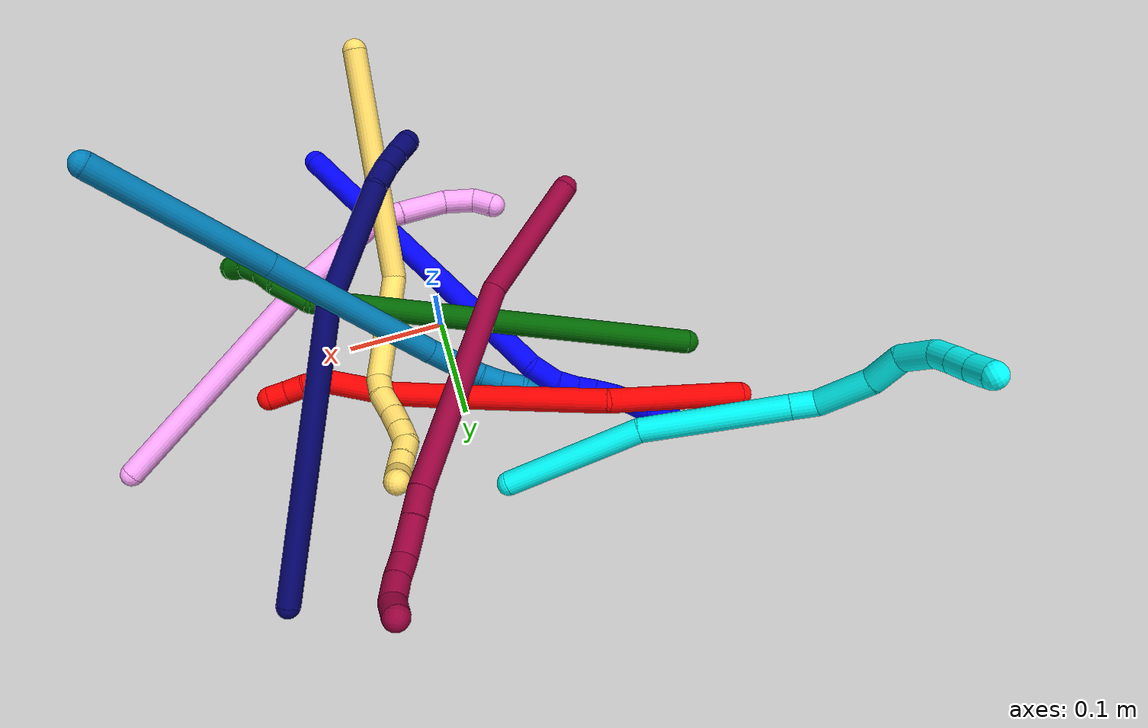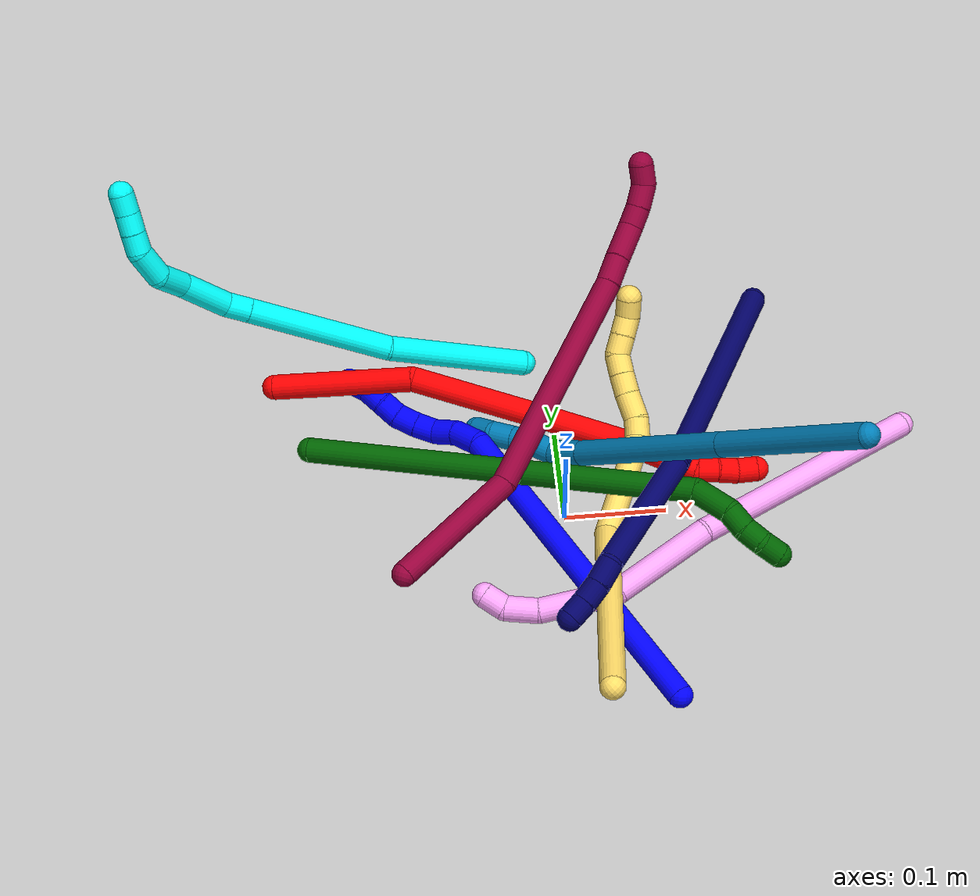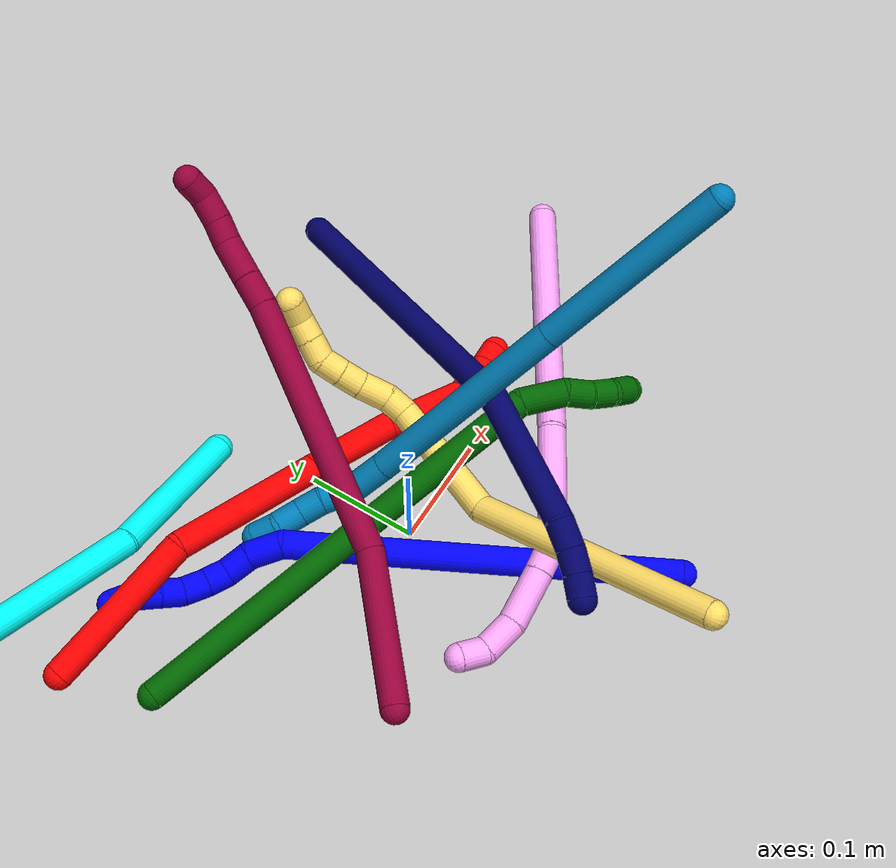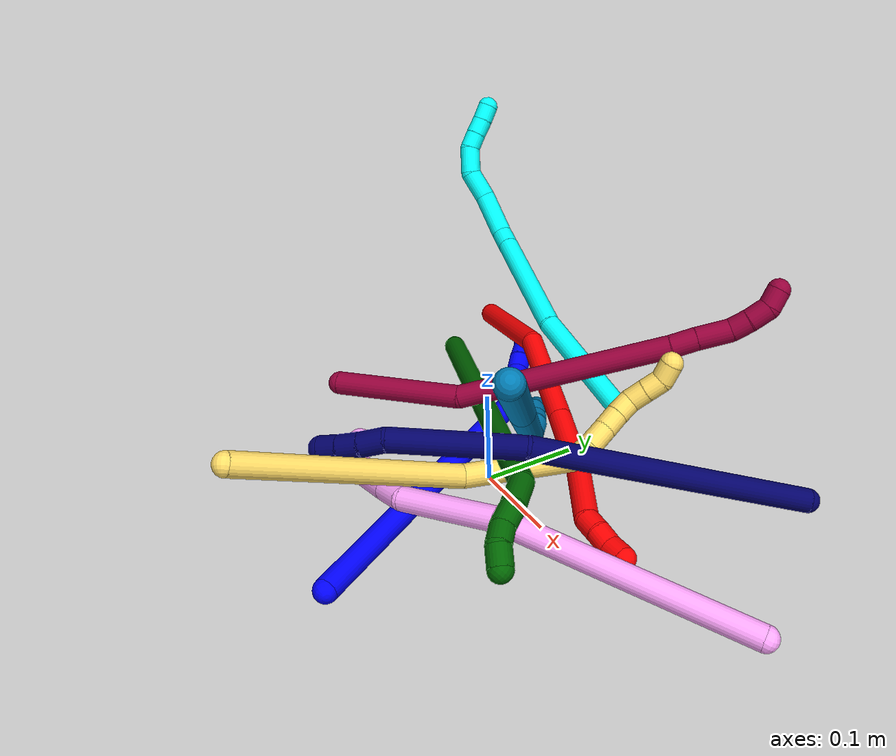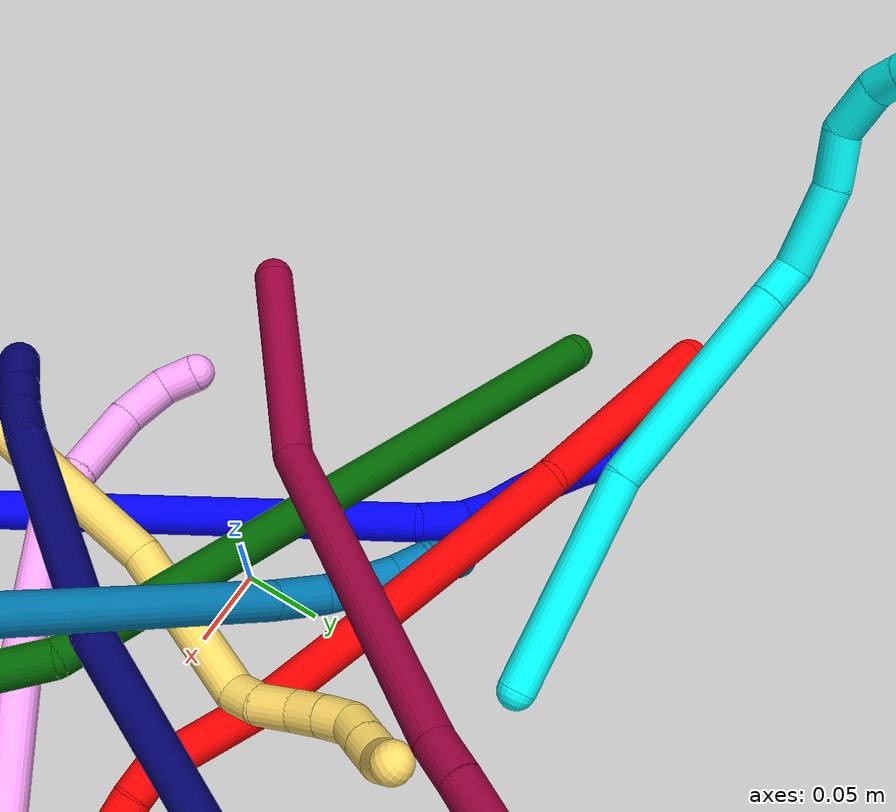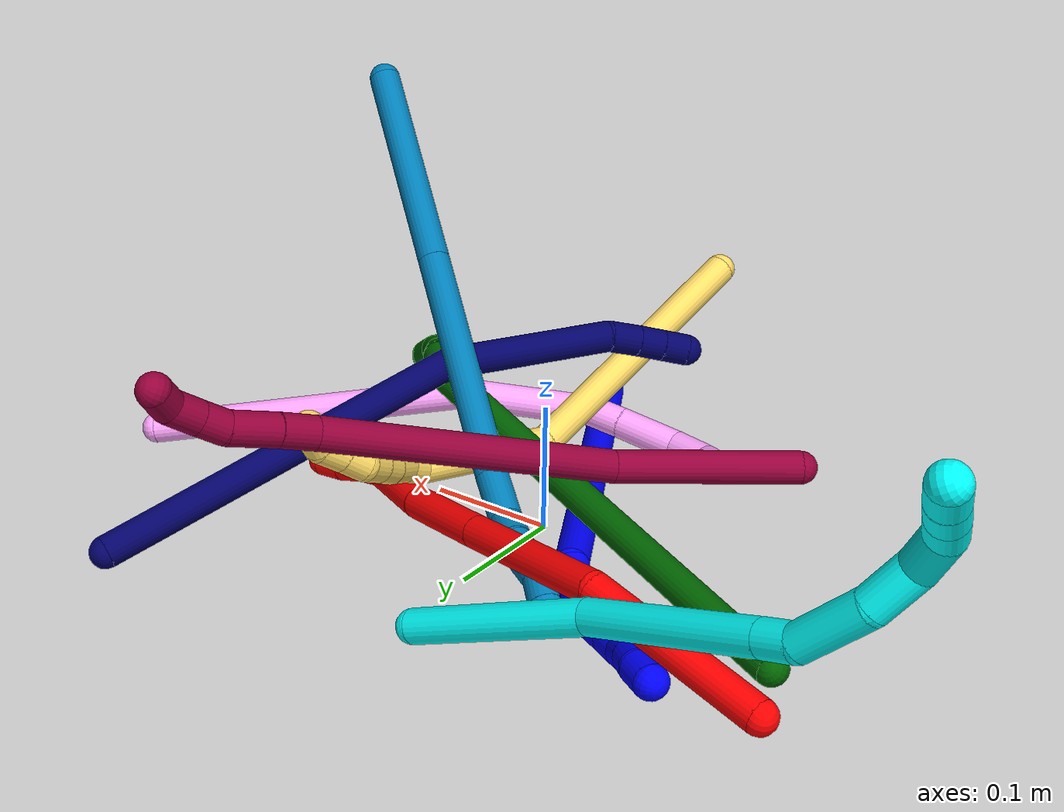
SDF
<sdf version="1.7">
 <world name="default">
  <plugin name="TubeGeneratorPlugin" filename="libtube_generator_plugin.so"/>
  <model name="photoneo_s_sensor">
   <static>1</static>
   <pose>0 0 2 1.57079 1.57079 3.14159</pose>
   <link name="link">
    <inertial><mass>0.1</mass></inertial>
    <sensor name="sensor" type="depth">
     <update_rate>30</update_rate>
     <camera>
      <horizontal_fov>1.22</horizontal_fov>
      <image><width>1920</width><height>1200</height><format>B8G8R8</format></image>
      <clip><near>0.1</near><far>4</far></clip>
      <depth_camera><output>points</output></depth_camera>
     </camera>
     <plugin name="camera_plugin" filename="libgazebo_ros_depth_camera.so">
      <baseline>0.2</baseline>
      <alwaysOn>1</alwaysOn>
      <updateRate>0.0</updateRate>
      <cameraName>camera_ir</cameraName>
      <imageTopicName>/camera/color/image_raw</imageTopicName>
      <cameraInfoTopicName>/camera/color/camera_info</cameraInfoTopicName>
      <depthImageTopicName>/camera/depth/image_raw</depthImageTopicName>
      <depthImageCameraInfoTopicName>/camera/depth/camera_info</depthImageCameraInfoTopicName>
      <pointCloudTopicName>/camera/depth/points</pointCloudTopicName>
      <frameName>fr_optical</frameName>
      <pointCloudCutoff>0.1</pointCloudCutoff>
      <pointCloudCutoffMax>2.0</pointCloudCutoffMax>
      <distortionK1>0</distortionK1>
      <distortionK2>0</distortionK2>
      <distortionK3>0</distortionK3>
      <distortionT1>0</distortionT1>
      <distortionT2>0</distortionT2>
      <CxPrime>0</CxPrime>
      <Cx>0</Cx>
      <Cy>0</Cy>
      <focalLength>0</focalLength>
      <hackBaseline>0</hackBaseline>
     </plugin>
    </sensor>
   </link>
  </model>
  <gravity>0 0 -9.8</gravity>
  <magnetic_field>6e-06 2.3e-05 -4.2e-05</magnetic_field>
  <atmosphere type="adiabatic"/>
  <physics name="default_physics" default="0" type="ode">
   <max_step_size>0.003</max_step_size>
   <real_time_factor>1</real_time_factor>
   <real_time_update_rate>1000</real_time_update_rate>
   <max_contacts>10000</max_contacts>
   <ode>
    <solver>
     <type>quick</type>
     <iters>100</iters>
     <sor>1.3</sor>
     <use_dynamic_moi_rescaling>0</use_dynamic_moi_rescaling>
    </solver>
    <constraints>
     <contact_max_correcting_vel>0</contact_max_correcting_vel>
     <contact_surface_layer>0.001</contact_surface_layer>
     <cfm>0</cfm>
     <erp>0.2</erp>
    </constraints>
   </ode>
  </physics>
  <scene><ambient>0.4 0.4 0.4 1</ambient><background>0.7 0.7 0.7 1</background><shadows>0</shadows></scene>
  <audio><device>default</device></audio>
  <spherical_coordinates>
   <surface_model>EARTH_WGS84</surface_model>
   <latitude_deg>0</latitude_deg>
   <longitude_deg>0</longitude_deg>
   <elevation>0</elevation>
   <heading_deg>0</heading_deg>
  </spherical_coordinates>
  <model name="bin">
   <static>1</static>
   <link name="bottom">
    <collision name="collision-bottom">
     <pose>0 0 -0.01 0 -0 0</pose>
     <geometry><box><size>0.8 0.6 0.02</size></box></geometry>
     <surface>
      <friction><ode><mu>100</mu><mu2>100</mu2></ode></friction>
      <contact><collide_bitmask>65535</collide_bitmask></contact>
     </surface>
    </collision>
   </link>
   <link name="west_wall">
    <collision name="collision-west_wall">
     <pose>-0.41 0 0.1 0 -0 0</pose>
     <geometry><box><size>0.02 0.6 0.2</size></box></geometry>
     <surface>
      <friction><ode><mu>100</mu><mu2>100</mu2></ode></friction>
      <contact><collide_bitmask>65535</collide_bitmask></contact>
     </surface>
    </collision>
   </link>
   <link name="east_wall">
    <collision name="collision-east_wall">
     <pose>0.41 0 0.1 0 -0 0</pose>
     <geometry><box><size>0.02 0.6 0.2</size></box></geometry>
     <surface>
      <friction><ode><mu>100</mu><mu2>100</mu2></ode></friction>
      <contact><collide_bitmask>65535</collide_bitmask></contact>
     </surface>
    </collision>
   </link>
   <link name="south_wall">
    <collision name="collision-south_wall">
     <pose>0 -0.31 0.1 0 -0 0</pose>
     <geometry><box><size>0.8 0.02 0.2</size></box></geometry>
     <surface>
      <friction><ode><mu>100</mu><mu2>100</mu2></ode></friction>
      <contact><collide_bitmask>65535</collide_bitmask></contact>
     </surface>
    </collision>
   </link>
   <link name="north_wall">
    <collision name="collision-north_wall">
     <pose>0 0.31 0.1 0 -0 0</pose>
     <geometry><box><size>0.8 0.02 0.2</size></box></geometry>
     <surface>
      <friction><ode><mu>100</mu><mu2>100</mu2></ode></friction>
      <contact><collide_bitmask>65535</collide_bitmask></contact>
     </surface>
    </collision>
   </link>
  </model>
  <model name="1">
   <static>0</static>
   <link name="1">
    <collision name="collision-cylinder-e_1_1_4">
     <pose>-0.072276 0.093438 -0.12329 -2.49308 -0.437072 1.16775</pose>
     <geometry><cylinder><radius>0.0125</radius><length>0.341495</length></cylinder></geometry>
     <surface>
      <friction><ode><mu>1.16</mu><mu2>1.16</mu2><slip1>0</slip1><slip2>0</slip2></ode></friction>
      <contact><ode><kp>1e+06</kp><kd>1</kd><max_vel>0</max_vel><min_depth>0.001</min_depth></ode></contact>
     </surface>
    </collision>
    <visual name="visual-cylinder-e_1_1_4">
     <pose>-0.072276 0.093438 -0.12329 -2.49308 -0.437072 1.16775</pose>
     <geometry><cylinder><radius>0.0125</radius><length>0.341495</length></cylinder></geometry>
     <material><ambient>0 0 1 1</ambient></material>
    </visual>
    <collision name="collision-cylinder-e_2_4_5">
     <pose>-0.144747 0.194857 -0.259523 -2.58898 -0.012894 0.045464</pose>
     <geometry><cylinder><radius>0.0125</radius><length>0.030415</length></cylinder></geometry>
     <surface>
      <friction><ode><mu>1.16</mu><mu2>1.16</mu2><slip1>0</slip1><slip2>0</slip2></ode></friction>
      <contact><ode><kp>1e+06</kp><kd>1</kd><max_vel>0</max_vel><min_depth>0.001</min_depth></ode></contact>
     </surface>
    </collision>
    <visual name="visual-cylinder-e_2_4_5">
     <pose>-0.144747 0.194857 -0.259523 -2.58898 -0.012894 0.045464</pose>
     <geometry><cylinder><radius>0.0125</radius><length>0.030415</length></cylinder></geometry>
     <material><ambient>0 0 1 1</ambient></material>
    </visual>
    <collision name="collision-cylinder-e_3_5_6">
     <pose>-0.142212 0.206642 -0.283809 -2.81814 0.224417 -1.20886</pose>
     <geometry><cylinder><radius>0.0125</radius><length>0.024543</length></cylinder></geometry>
     <surface>
      <friction><ode><mu>1.16</mu><mu2>1.16</mu2><slip1>0</slip1><slip2>0</slip2></ode></friction>
      <contact><ode><kp>1e+06</kp><kd>1</kd><max_vel>0</max_vel><min_depth>0.001</min_depth></ode></contact>
     </surface>
    </collision>
    <visual name="visual-cylinder-e_3_5_6">
     <pose>-0.142212 0.206642 -0.283809 -2.81814 0.224417 -1.20886</pose>
     <geometry><cylinder><radius>0.0125</radius><length>0.024543</length></cylinder></geometry>
     <material><ambient>0 0 1 1</ambient></material>
    </visual>
    <collision name="collision-cylinder-e_4_6_7">
     <pose>-0.141087 0.211397 -0.305337 -3.0483 -0.155736 2.06333</pose>
     <geometry><cylinder><radius>0.0125</radius><length>0.020708</length></cylinder></geometry>
     <surface>
      <friction><ode><mu>1.16</mu><mu2>1.16</mu2><slip1>0</slip1><slip2>0</slip2></ode></friction>
      <contact><ode><kp>1e+06</kp><kd>1</kd><max_vel>0</max_vel><min_depth>0.001</min_depth></ode></contact>
     </surface>
    </collision>
    <visual name="visual-cylinder-e_4_6_7">
     <pose>-0.141087 0.211397 -0.305337 -3.0483 -0.155736 2.06333</pose>
     <geometry><cylinder><radius>0.0125</radius><length>0.020708</length></cylinder></geometry>
     <material><ambient>0 0 1 1</ambient></material>
    </visual>
    <collision name="collision-cylinder-e_5_7_8">
     <pose>-0.145472 0.213757 -0.326001 -3.00815 -0.256975 2.187</pose>
     <geometry><cylinder><radius>0.0125</radius><length>0.021867</length></cylinder></geometry>
     <surface>
      <friction><ode><mu>1.16</mu><mu2>1.16</mu2><slip1>0</slip1><slip2>0</slip2></ode></friction>
      <contact><ode><kp>1e+06</kp><kd>1</kd><max_vel>0</max_vel><min_depth>0.001</min_depth></ode></contact>
     </surface>
    </collision>
    <visual name="visual-cylinder-e_5_7_8">
     <pose>-0.145472 0.213757 -0.326001 -3.00815 -0.256975 2.187</pose>
     <geometry><cylinder><radius>0.0125</radius><length>0.021867</length></cylinder></geometry>
     <material><ambient>0 0 1 1</ambient></material>
    </visual>
    <collision name="collision-cylinder-e_6_8_9">
     <pose>-0.153625 0.21658 -0.344872 -2.97439 -0.563301 2.5778</pose>
     <geometry><cylinder><radius>0.0125</radius><length>0.020128</length></cylinder></geometry>
     <surface>
      <friction><ode><mu>1.16</mu><mu2>1.16</mu2><slip1>0</slip1><slip2>0</slip2></ode></friction>
      <contact><ode><kp>1e+06</kp><kd>1</kd><max_vel>0</max_vel><min_depth>0.001</min_depth></ode></contact>
     </surface>
    </collision>
    <visual name="visual-cylinder-e_6_8_9">
     <pose>-0.153625 0.21658 -0.344872 -2.97439 -0.563301 2.5778</pose>
     <geometry><cylinder><radius>0.0125</radius><length>0.020128</length></cylinder></geometry>
     <material><ambient>0 0 1 1</ambient></material>
    </visual>
    <collision name="collision-cylinder-e_7_9_10">
     <pose>-0.16379 0.220578 -0.361925 -2.85185 -0.487438 2.08042</pose>
     <geometry><cylinder><radius>0.0125</radius><length>0.020461</length></cylinder></geometry>
     <surface>
      <friction><ode><mu>1.16</mu><mu2>1.16</mu2><slip1>0</slip1><slip2>0</slip2></ode></friction>
      <contact><ode><kp>1e+06</kp><kd>1</kd><max_vel>0</max_vel><min_depth>0.001</min_depth></ode></contact>
     </surface>
    </collision>
    <visual name="visual-cylinder-e_7_9_10">
     <pose>-0.16379 0.220578 -0.361925 -2.85185 -0.487438 2.08042</pose>
     <geometry><cylinder><radius>0.0125</radius><length>0.020461</length></cylinder></geometry>
     <material><ambient>0 0 1 1</ambient></material>
    </visual>
    <collision name="collision-cylinder-e_8_10_2">
     <pose>-0.170946 0.224917 -0.380343 -2.96351 -0.234151 1.84305</pose>
     <geometry><cylinder><radius>0.0125</radius><length>0.020383</length></cylinder></geometry>
     <surface>
      <friction><ode><mu>1.16</mu><mu2>1.16</mu2><slip1>0</slip1><slip2>0</slip2></ode></friction>
      <contact><ode><kp>1e+06</kp><kd>1</kd><max_vel>0</max_vel><min_depth>0.001</min_depth></ode></contact>
     </surface>
    </collision>
    <visual name="visual-cylinder-e_8_10_2">
     <pose>-0.170946 0.224917 -0.380343 -2.96351 -0.234151 1.84305</pose>
     <geometry><cylinder><radius>0.0125</radius><length>0.020383</length></cylinder></geometry>
     <material><ambient>0 0 1 1</ambient></material>
    </visual>
    <collision name="collision-sphere-2">
     <pose>-0.173311 0.226673 -0.3901 0 -0 0</pose>
     <geometry><sphere><radius>0.0125</radius></sphere></geometry>
     <surface>
      <friction><ode><mu>1.16</mu><mu2>1.16</mu2><slip1>0</slip1><slip2>0</slip2></ode></friction>
      <contact><ode><kp>1e+06</kp><kd>1</kd><max_vel>0</max_vel><min_depth>0.001</min_depth></ode></contact>
     </surface>
    </collision>
    <visual name="visual-sphere-2">
     <pose>-0.173311 0.226673 -0.3901 0 -0 0</pose>
     <geometry><sphere><radius>0.0125</radius></sphere></geometry>
     <material><ambient>0 0 1 1</ambient></material>
    </visual>
    <collision name="collision-sphere-10">
     <pose>-0.168582 0.223161 -0.370587 0 -0 0</pose>
     <geometry><sphere><radius>0.0125</radius></sphere></geometry>
     <surface>
      <friction><ode><mu>1.16</mu><mu2>1.16</mu2><slip1>0</slip1><slip2>0</slip2></ode></friction>
      <contact><ode><kp>1e+06</kp><kd>1</kd><max_vel>0</max_vel><min_depth>0.001</min_depth></ode></contact>
     </surface>
    </collision>
    <visual name="visual-sphere-10">
     <pose>-0.168582 0.223161 -0.370587 0 -0 0</pose>
     <geometry><sphere><radius>0.0125</radius></sphere></geometry>
     <material><ambient>0 0 1 1</ambient></material>
    </visual>
    <collision name="collision-sphere-9">
     <pose>-0.158999 0.217996 -0.353262 0 -0 0</pose>
     <geometry><sphere><radius>0.0125</radius></sphere></geometry>
     <surface>
      <friction><ode><mu>1.16</mu><mu2>1.16</mu2><slip1>0</slip1><slip2>0</slip2></ode></friction>
      <contact><ode><kp>1e+06</kp><kd>1</kd><max_vel>0</max_vel><min_depth>0.001</min_depth></ode></contact>
     </surface>
    </collision>
    <visual name="visual-sphere-9">
     <pose>-0.158999 0.217996 -0.353262 0 -0 0</pose>
     <geometry><sphere><radius>0.0125</radius></sphere></geometry>
     <material><ambient>0 0 1 1</ambient></material>
    </visual>
    <collision name="collision-sphere-4">
     <pose>-0.144551 0.186875 -0.24658 0 -0 0</pose>
     <geometry><sphere><radius>0.0125</radius></sphere></geometry>
     <surface>
      <friction><ode><mu>1.16</mu><mu2>1.16</mu2><slip1>0</slip1><slip2>0</slip2></ode></friction>
      <contact><ode><kp>1e+06</kp><kd>1</kd><max_vel>0</max_vel><min_depth>0.001</min_depth></ode></contact>
     </surface>
    </collision>
    <visual name="visual-sphere-4">
     <pose>-0.144551 0.186875 -0.24658 0 -0 0</pose>
     <geometry><sphere><radius>0.0125</radius></sphere></geometry>
     <material><ambient>0 0 1 1</ambient></material>
    </visual>
    <collision name="collision-sphere-1">
     <geometry><sphere><radius>0.0125</radius></sphere></geometry>
     <surface>
      <friction><ode><mu>1.16</mu><mu2>1.16</mu2><slip1>0</slip1><slip2>0</slip2></ode></friction>
      <contact><ode><kp>1e+06</kp><kd>1</kd><max_vel>0</max_vel><min_depth>0.001</min_depth></ode></contact>
     </surface>
    </collision>
    <visual name="visual-sphere-1">
     <geometry><sphere><radius>0.0125</radius></sphere></geometry>
     <material><ambient>0 0 1 1</ambient></material>
    </visual>
    <collision name="collision-sphere-8">
     <pose>-0.148251 0.215164 -0.336482 0 -0 0</pose>
     <geometry><sphere><radius>0.0125</radius></sphere></geometry>
     <surface>
      <friction><ode><mu>1.16</mu><mu2>1.16</mu2><slip1>0</slip1><slip2>0</slip2></ode></friction>
      <contact><ode><kp>1e+06</kp><kd>1</kd><max_vel>0</max_vel><min_depth>0.001</min_depth></ode></contact>
     </surface>
    </collision>
    <visual name="visual-sphere-8">
     <pose>-0.148251 0.215164 -0.336482 0 -0 0</pose>
     <geometry><sphere><radius>0.0125</radius></sphere></geometry>
     <material><ambient>0 0 1 1</ambient></material>
    </visual>
    <collision name="collision-sphere-5">
     <pose>-0.144943 0.202839 -0.272466 0 -0 0</pose>
     <geometry><sphere><radius>0.0125</radius></sphere></geometry>
     <surface>
      <friction><ode><mu>1.16</mu><mu2>1.16</mu2><slip1>0</slip1><slip2>0</slip2></ode></friction>
      <contact><ode><kp>1e+06</kp><kd>1</kd><max_vel>0</max_vel><min_depth>0.001</min_depth></ode></contact>
     </surface>
    </collision>
    <visual name="visual-sphere-5">
     <pose>-0.144943 0.202839 -0.272466 0 -0 0</pose>
     <geometry><sphere><radius>0.0125</radius></sphere></geometry>
     <material><ambient>0 0 1 1</ambient></material>
    </visual>
    <collision name="collision-sphere-6">
     <pose>-0.139481 0.210444 -0.295153 0 -0 0</pose>
     <geometry><sphere><radius>0.0125</radius></sphere></geometry>
     <surface>
      <friction><ode><mu>1.16</mu><mu2>1.16</mu2><slip1>0</slip1><slip2>0</slip2></ode></friction>
      <contact><ode><kp>1e+06</kp><kd>1</kd><max_vel>0</max_vel><min_depth>0.001</min_depth></ode></contact>
     </surface>
    </collision>
    <visual name="visual-sphere-6">
     <pose>-0.139481 0.210444 -0.295153 0 -0 0</pose>
     <geometry><sphere><radius>0.0125</radius></sphere></geometry>
     <material><ambient>0 0 1 1</ambient></material>
    </visual>
    <collision name="collision-sphere-7">
     <pose>-0.142693 0.21235 -0.315521 0 -0 0</pose>
     <geometry><sphere><radius>0.0125</radius></sphere></geometry>
     <surface>
      <friction><ode><mu>1.16</mu><mu2>1.16</mu2><slip1>0</slip1><slip2>0</slip2></ode></friction>
      <contact><ode><kp>1e+06</kp><kd>1</kd><max_vel>0</max_vel><min_depth>0.001</min_depth></ode></contact>
     </surface>
    </collision>
    <visual name="visual-sphere-7">
     <pose>-0.142693 0.21235 -0.315521 0 -0 0</pose>
     <geometry><sphere><radius>0.0125</radius></sphere></geometry>
     <material><ambient>0 0 1 1</ambient></material>
    </visual>
    <inertial>
     <pose>-0.09721 0.130831 -0.185026 0 -0 0</pose>
     <mass>0.5</mass>
     <inertia>
      <ixx>0.003952</ixx>
      <ixy>0</ixy>
      <ixz>0</ixz>
      <iyy>0.002542</iyy>
      <iyz>0</iyz>
      <izz>-0.000445</izz>
     </inertia>
    </inertial>
   </link>
   <pose>0.085963 -0.221271 0.011486 -1.49456 1.03007 -1.81535</pose>
  </model>
  <model name="2">
   <static>0</static>
   <link name="2">
    <collision name="collision-cylinder-e_1_1_4">
     <pose>0.067923 -0.008934 -0.020213 2.7254 1.25623 2.5757</pose>
     <geometry><cylinder><radius>0.0125</radius><length>0.142855</length></cylinder></geometry>
     <surface>
      <friction><ode><mu>1.16</mu><mu2>1.16</mu2><slip1>0</slip1><slip2>0</slip2></ode></friction>
      <contact><ode><kp>1e+06</kp><kd>1</kd><max_vel>0</max_vel><min_depth>0.001</min_depth></ode></contact>
     </surface>
    </collision>
    <visual name="visual-cylinder-e_1_1_4">
     <pose>0.067923 -0.008934 -0.020213 2.7254 1.25623 2.5757</pose>
     <geometry><cylinder><radius>0.0125</radius><length>0.142855</length></cylinder></geometry>
     <material><ambient>1 0 0 1</ambient></material>
    </visual>
    <collision name="collision-cylinder-e_2_4_5">
     <pose>0.189216 -0.029743 -0.083572 2.87303 0.873043 2.57788</pose>
     <geometry><cylinder><radius>0.0125</radius><length>0.139298</length></cylinder></geometry>
     <surface>
      <friction><ode><mu>1.16</mu><mu2>1.16</mu2><slip1>0</slip1><slip2>0</slip2></ode></friction>
      <contact><ode><kp>1e+06</kp><kd>1</kd><max_vel>0</max_vel><min_depth>0.001</min_depth></ode></contact>
     </surface>
    </collision>
    <visual name="visual-cylinder-e_2_4_5">
     <pose>0.189216 -0.029743 -0.083572 2.87303 0.873043 2.57788</pose>
     <geometry><cylinder><radius>0.0125</radius><length>0.139298</length></cylinder></geometry>
     <material><ambient>1 0 0 1</ambient></material>
    </visual>
    <collision name="collision-cylinder-e_3_5_6">
     <pose>0.274092 -0.049236 -0.152326 2.85241 0.8674 2.53234</pose>
     <geometry><cylinder><radius>0.0125</radius><length>0.082618</length></cylinder></geometry>
     <surface>
      <friction><ode><mu>1.16</mu><mu2>1.16</mu2><slip1>0</slip1><slip2>0</slip2></ode></friction>
      <contact><ode><kp>1e+06</kp><kd>1</kd><max_vel>0</max_vel><min_depth>0.001</min_depth></ode></contact>
     </surface>
    </collision>
    <visual name="visual-cylinder-e_3_5_6">
     <pose>0.274092 -0.049236 -0.152326 2.85241 0.8674 2.53234</pose>
     <geometry><cylinder><radius>0.0125</radius><length>0.082618</length></cylinder></geometry>
     <material><ambient>1 0 0 1</ambient></material>
    </visual>
    <collision name="collision-cylinder-e_4_6_7">
     <pose>0.333091 -0.068836 -0.200091 2.64586 0.82919 2.09789</pose>
     <geometry><cylinder><radius>0.0125</radius><length>0.074575</length></cylinder></geometry>
     <surface>
      <friction><ode><mu>1.16</mu><mu2>1.16</mu2><slip1>0</slip1><slip2>0</slip2></ode></friction>
      <contact><ode><kp>1e+06</kp><kd>1</kd><max_vel>0</max_vel><min_depth>0.001</min_depth></ode></contact>
     </surface>
    </collision>
    <visual name="visual-cylinder-e_4_6_7">
     <pose>0.333091 -0.068836 -0.200091 2.64586 0.82919 2.09789</pose>
     <geometry><cylinder><radius>0.0125</radius><length>0.074575</length></cylinder></geometry>
     <material><ambient>1 0 0 1</ambient></material>
    </visual>
    <collision name="collision-cylinder-e_5_7_8">
     <pose>0.369316 -0.079798 -0.227268 -2.94136 1.03995 -2.79423</pose>
     <geometry><cylinder><radius>0.0125</radius><length>0.020245</length></cylinder></geometry>
     <surface>
      <friction><ode><mu>1.16</mu><mu2>1.16</mu2><slip1>0</slip1><slip2>0</slip2></ode></friction>
      <contact><ode><kp>1e+06</kp><kd>1</kd><max_vel>0</max_vel><min_depth>0.001</min_depth></ode></contact>
     </surface>
    </collision>
    <visual name="visual-cylinder-e_5_7_8">
     <pose>0.369316 -0.079798 -0.227268 -2.94136 1.03995 -2.79423</pose>
     <geometry><cylinder><radius>0.0125</radius><length>0.020245</length></cylinder></geometry>
     <material><ambient>1 0 0 1</ambient></material>
    </visual>
    <collision name="collision-cylinder-e_6_8_9">
     <pose>0.385842 -0.076824 -0.238487 -2.83602 0.875992 -2.50627</pose>
     <geometry><cylinder><radius>0.0125</radius><length>0.020299</length></cylinder></geometry>
     <surface>
      <friction><ode><mu>1.16</mu><mu2>1.16</mu2><slip1>0</slip1><slip2>0</slip2></ode></friction>
      <contact><ode><kp>1e+06</kp><kd>1</kd><max_vel>0</max_vel><min_depth>0.001</min_depth></ode></contact>
     </surface>
    </collision>
    <visual name="visual-cylinder-e_6_8_9">
     <pose>0.385842 -0.076824 -0.238487 -2.83602 0.875992 -2.50627</pose>
     <geometry><cylinder><radius>0.0125</radius><length>0.020299</length></cylinder></geometry>
     <material><ambient>1 0 0 1</ambient></material>
    </visual>
    <collision name="collision-cylinder-e_7_9_2">
     <pose>0.402581 -0.073209 -0.248972 -2.77225 1.09583 -2.5475</pose>
     <geometry><cylinder><radius>0.0125</radius><length>0.020111</length></cylinder></geometry>
     <surface>
      <friction><ode><mu>1.16</mu><mu2>1.16</mu2><slip1>0</slip1><slip2>0</slip2></ode></friction>
      <contact><ode><kp>1e+06</kp><kd>1</kd><max_vel>0</max_vel><min_depth>0.001</min_depth></ode></contact>
     </surface>
    </collision>
    <visual name="visual-cylinder-e_7_9_2">
     <pose>0.402581 -0.073209 -0.248972 -2.77225 1.09583 -2.5475</pose>
     <geometry><cylinder><radius>0.0125</radius><length>0.020111</length></cylinder></geometry>
     <material><ambient>1 0 0 1</ambient></material>
    </visual>
    <collision name="collision-sphere-2">
     <pose>0.411523 -0.071549 -0.25326 0 -0 0</pose>
     <geometry><sphere><radius>0.0125</radius></sphere></geometry>
     <surface>
      <friction><ode><mu>1.16</mu><mu2>1.16</mu2><slip1>0</slip1><slip2>0</slip2></ode></friction>
      <contact><ode><kp>1e+06</kp><kd>1</kd><max_vel>0</max_vel><min_depth>0.001</min_depth></ode></contact>
     </surface>
    </collision>
    <visual name="visual-sphere-2">
     <pose>0.411523 -0.071549 -0.25326 0 -0 0</pose>
     <geometry><sphere><radius>0.0125</radius></sphere></geometry>
     <material><ambient>1 0 0 1</ambient></material>
    </visual>
    <collision name="collision-sphere-9">
     <pose>0.393638 -0.074869 -0.244684 0 -0 0</pose>
     <geometry><sphere><radius>0.0125</radius></sphere></geometry>
     <surface>
      <friction><ode><mu>1.16</mu><mu2>1.16</mu2><slip1>0</slip1><slip2>0</slip2></ode></friction>
      <contact><ode><kp>1e+06</kp><kd>1</kd><max_vel>0</max_vel><min_depth>0.001</min_depth></ode></contact>
     </surface>
    </collision>
    <visual name="visual-sphere-9">
     <pose>0.393638 -0.074869 -0.244684 0 -0 0</pose>
     <geometry><sphere><radius>0.0125</radius></sphere></geometry>
     <material><ambient>1 0 0 1</ambient></material>
    </visual>
    <collision name="collision-sphere-4">
     <pose>0.135845 -0.017869 -0.040426 0 -0 0</pose>
     <geometry><sphere><radius>0.0125</radius></sphere></geometry>
     <surface>
      <friction><ode><mu>1.16</mu><mu2>1.16</mu2><slip1>0</slip1><slip2>0</slip2></ode></friction>
      <contact><ode><kp>1e+06</kp><kd>1</kd><max_vel>0</max_vel><min_depth>0.001</min_depth></ode></contact>
     </surface>
    </collision>
    <visual name="visual-sphere-4">
     <pose>0.135845 -0.017869 -0.040426 0 -0 0</pose>
     <geometry><sphere><radius>0.0125</radius></sphere></geometry>
     <material><ambient>1 0 0 1</ambient></material>
    </visual>
    <collision name="collision-sphere-1">
     <geometry><sphere><radius>0.0125</radius></sphere></geometry>
     <surface>
      <friction><ode><mu>1.16</mu><mu2>1.16</mu2><slip1>0</slip1><slip2>0</slip2></ode></friction>
      <contact><ode><kp>1e+06</kp><kd>1</kd><max_vel>0</max_vel><min_depth>0.001</min_depth></ode></contact>
     </surface>
    </collision>
    <visual name="visual-sphere-1">
     <geometry><sphere><radius>0.0125</radius></sphere></geometry>
     <material><ambient>1 0 0 1</ambient></material>
    </visual>
    <collision name="collision-sphere-8">
     <pose>0.378045 -0.078778 -0.23229 0 -0 0</pose>
     <geometry><sphere><radius>0.0125</radius></sphere></geometry>
     <surface>
      <friction><ode><mu>1.16</mu><mu2>1.16</mu2><slip1>0</slip1><slip2>0</slip2></ode></friction>
      <contact><ode><kp>1e+06</kp><kd>1</kd><max_vel>0</max_vel><min_depth>0.001</min_depth></ode></contact>
     </surface>
    </collision>
    <visual name="visual-sphere-8">
     <pose>0.378045 -0.078778 -0.23229 0 -0 0</pose>
     <geometry><sphere><radius>0.0125</radius></sphere></geometry>
     <material><ambient>1 0 0 1</ambient></material>
    </visual>
    <collision name="collision-sphere-5">
     <pose>0.242588 -0.041617 -0.126717 0 -0 0</pose>
     <geometry><sphere><radius>0.0125</radius></sphere></geometry>
     <surface>
      <friction><ode><mu>1.16</mu><mu2>1.16</mu2><slip1>0</slip1><slip2>0</slip2></ode></friction>
      <contact><ode><kp>1e+06</kp><kd>1</kd><max_vel>0</max_vel><min_depth>0.001</min_depth></ode></contact>
     </surface>
    </collision>
    <visual name="visual-sphere-5">
     <pose>0.242588 -0.041617 -0.126717 0 -0 0</pose>
     <geometry><sphere><radius>0.0125</radius></sphere></geometry>
     <material><ambient>1 0 0 1</ambient></material>
    </visual>
    <collision name="collision-sphere-6">
     <pose>0.305596 -0.056856 -0.177936 0 -0 0</pose>
     <geometry><sphere><radius>0.0125</radius></sphere></geometry>
     <surface>
      <friction><ode><mu>1.16</mu><mu2>1.16</mu2><slip1>0</slip1><slip2>0</slip2></ode></friction>
      <contact><ode><kp>1e+06</kp><kd>1</kd><max_vel>0</max_vel><min_depth>0.001</min_depth></ode></contact>
     </surface>
    </collision>
    <visual name="visual-sphere-6">
     <pose>0.305596 -0.056856 -0.177936 0 -0 0</pose>
     <geometry><sphere><radius>0.0125</radius></sphere></geometry>
     <material><ambient>1 0 0 1</ambient></material>
    </visual>
    <collision name="collision-sphere-7">
     <pose>0.360587 -0.080817 -0.222246 0 -0 0</pose>
     <geometry><sphere><radius>0.0125</radius></sphere></geometry>
     <surface>
      <friction><ode><mu>1.16</mu><mu2>1.16</mu2><slip1>0</slip1><slip2>0</slip2></ode></friction>
      <contact><ode><kp>1e+06</kp><kd>1</kd><max_vel>0</max_vel><min_depth>0.001</min_depth></ode></contact>
     </surface>
    </collision>
    <visual name="visual-sphere-7">
     <pose>0.360587 -0.080817 -0.222246 0 -0 0</pose>
     <geometry><sphere><radius>0.0125</radius></sphere></geometry>
     <material><ambient>1 0 0 1</ambient></material>
    </visual>
    <inertial>
     <pose>0.213901 -0.038536 -0.112969 0 -0 0</pose>
     <mass>0.5</mass>
     <inertia>
      <ixx>-4e-05</ixx>
      <ixy>0</ixy>
      <ixz>0</ixz>
      <iyy>0.000688</iyy>
      <iyz>0</iyz>
      <izz>-0.000412</izz>
     </inertia>
    </inertial>
   </link>
   <pose>-0.2754 0.165052 0.031993 -0.344242 -0.435833 0.042088</pose>
  </model>
  <model name="3">
   <static>0</static>
   <link name="3">
    <collision name="collision-cylinder-e_1_1_4">
     <pose>-0.007158 -0.007054 0.072229 0.097349 -0.098317 -0.004793</pose>
     <geometry><cylinder><radius>0.0125</radius><length>0.145849</length></cylinder></geometry>
     <surface>
      <friction><ode><mu>1.16</mu><mu2>1.16</mu2><slip1>0</slip1><slip2>0</slip2></ode></friction>
      <contact><ode><kp>1e+06</kp><kd>1</kd><max_vel>0</max_vel><min_depth>0.001</min_depth></ode></contact>
     </surface>
    </collision>
    <visual name="visual-cylinder-e_1_1_4">
     <pose>-0.007158 -0.007054 0.072229 0.097349 -0.098317 -0.004793</pose>
     <geometry><cylinder><radius>0.0125</radius><length>0.145849</length></cylinder></geometry>
     <material><ambient>0.003922 1 0.996078 1</ambient></material>
    </visual>
    <collision name="collision-cylinder-e_2_4_5">
     <pose>-0.035167 -0.012439 0.213684 -0.02409 -0.292469 0.003548</pose>
     <geometry><cylinder><radius>0.0125</radius><length>0.144635</length></cylinder></geometry>
     <surface>
      <friction><ode><mu>1.16</mu><mu2>1.16</mu2><slip1>0</slip1><slip2>0</slip2></ode></friction>
      <contact><ode><kp>1e+06</kp><kd>1</kd><max_vel>0</max_vel><min_depth>0.001</min_depth></ode></contact>
     </surface>
    </collision>
    <visual name="visual-cylinder-e_2_4_5">
     <pose>-0.035167 -0.012439 0.213684 -0.02409 -0.292469 0.003548</pose>
     <geometry><cylinder><radius>0.0125</radius><length>0.144635</length></cylinder></geometry>
     <material><ambient>0.003922 1 0.996078 1</ambient></material>
    </visual>
    <collision name="collision-cylinder-e_3_5_6">
     <pose>-0.059769 -0.010614 0.294655 -0.01344 -0.309194 0.002095</pose>
     <geometry><cylinder><radius>0.0125</radius><length>0.024661</length></cylinder></geometry>
     <surface>
      <friction><ode><mu>1.16</mu><mu2>1.16</mu2><slip1>0</slip1><slip2>0</slip2></ode></friction>
      <contact><ode><kp>1e+06</kp><kd>1</kd><max_vel>0</max_vel><min_depth>0.001</min_depth></ode></contact>
     </surface>
    </collision>
    <visual name="visual-cylinder-e_3_5_6">
     <pose>-0.059769 -0.010614 0.294655 -0.01344 -0.309194 0.002095</pose>
     <geometry><cylinder><radius>0.0125</radius><length>0.024661</length></cylinder></geometry>
     <material><ambient>0.003922 1 0.996078 1</ambient></material>
    </visual>
    <collision name="collision-cylinder-e_4_6_7">
     <pose>-0.060181 -0.004611 0.3335 -0.212418 0.119902 -0.012798</pose>
     <geometry><cylinder><radius>0.0125</radius><length>0.055848</length></cylinder></geometry>
     <surface>
      <friction><ode><mu>1.16</mu><mu2>1.16</mu2><slip1>0</slip1><slip2>0</slip2></ode></friction>
      <contact><ode><kp>1e+06</kp><kd>1</kd><max_vel>0</max_vel><min_depth>0.001</min_depth></ode></contact>
     </surface>
    </collision>
    <visual name="visual-cylinder-e_4_6_7">
     <pose>-0.060181 -0.004611 0.3335 -0.212418 0.119902 -0.012798</pose>
     <geometry><cylinder><radius>0.0125</radius><length>0.055848</length></cylinder></geometry>
     <material><ambient>0.003922 1 0.996078 1</ambient></material>
    </visual>
    <collision name="collision-cylinder-e_5_7_8">
     <pose>-0.049823 0.004176 0.376448 -0.183592 0.41064 -0.038337</pose>
     <geometry><cylinder><radius>0.0125</radius><length>0.035161</length></cylinder></geometry>
     <surface>
      <friction><ode><mu>1.16</mu><mu2>1.16</mu2><slip1>0</slip1><slip2>0</slip2></ode></friction>
      <contact><ode><kp>1e+06</kp><kd>1</kd><max_vel>0</max_vel><min_depth>0.001</min_depth></ode></contact>
     </surface>
    </collision>
    <visual name="visual-cylinder-e_5_7_8">
     <pose>-0.049823 0.004176 0.376448 -0.183592 0.41064 -0.038337</pose>
     <geometry><cylinder><radius>0.0125</radius><length>0.035161</length></cylinder></geometry>
     <material><ambient>0.003922 1 0.996078 1</ambient></material>
    </visual>
    <collision name="collision-cylinder-e_6_8_9">
     <pose>-0.041155 0.016782 0.405927 -0.616689 0.098449 -0.031379</pose>
     <geometry><cylinder><radius>0.0125</radius><length>0.033579</length></cylinder></geometry>
     <surface>
      <friction><ode><mu>1.16</mu><mu2>1.16</mu2><slip1>0</slip1><slip2>0</slip2></ode></friction>
      <contact><ode><kp>1e+06</kp><kd>1</kd><max_vel>0</max_vel><min_depth>0.001</min_depth></ode></contact>
     </surface>
    </collision>
    <visual name="visual-cylinder-e_6_8_9">
     <pose>-0.041155 0.016782 0.405927 -0.616689 0.098449 -0.031379</pose>
     <geometry><cylinder><radius>0.0125</radius><length>0.033579</length></cylinder></geometry>
     <material><ambient>0.003922 1 0.996078 1</ambient></material>
    </visual>
    <collision name="collision-cylinder-e_7_9_10">
     <pose>-0.040279 0.034973 0.424895 -1.01153 -0.076786 0.04254</pose>
     <geometry><cylinder><radius>0.0125</radius><length>0.020181</length></cylinder></geometry>
     <surface>
      <friction><ode><mu>1.16</mu><mu2>1.16</mu2><slip1>0</slip1><slip2>0</slip2></ode></friction>
      <contact><ode><kp>1e+06</kp><kd>1</kd><max_vel>0</max_vel><min_depth>0.001</min_depth></ode></contact>
     </surface>
    </collision>
    <visual name="visual-cylinder-e_7_9_10">
     <pose>-0.040279 0.034973 0.424895 -1.01153 -0.076786 0.04254</pose>
     <geometry><cylinder><radius>0.0125</radius><length>0.020181</length></cylinder></geometry>
     <material><ambient>0.003922 1 0.996078 1</ambient></material>
    </visual>
    <collision name="collision-cylinder-e_8_10_11">
     <pose>-0.042185 0.052124 0.435247 -1.04413 -0.112987 0.065049</pose>
     <geometry><cylinder><radius>0.0125</radius><length>0.020078</length></cylinder></geometry>
     <surface>
      <friction><ode><mu>1.16</mu><mu2>1.16</mu2><slip1>0</slip1><slip2>0</slip2></ode></friction>
      <contact><ode><kp>1e+06</kp><kd>1</kd><max_vel>0</max_vel><min_depth>0.001</min_depth></ode></contact>
     </surface>
    </collision>
    <visual name="visual-cylinder-e_8_10_11">
     <pose>-0.042185 0.052124 0.435247 -1.04413 -0.112987 0.065049</pose>
     <geometry><cylinder><radius>0.0125</radius><length>0.020078</length></cylinder></geometry>
     <material><ambient>0.003922 1 0.996078 1</ambient></material>
    </visual>
    <collision name="collision-cylinder-e_9_11_2">
     <pose>-0.043895 0.069189 0.445599 -1.00688 -0.057857 0.031873</pose>
     <geometry><cylinder><radius>0.0125</radius><length>0.020009</length></cylinder></geometry>
     <surface>
      <friction><ode><mu>1.16</mu><mu2>1.16</mu2><slip1>0</slip1><slip2>0</slip2></ode></friction>
      <contact><ode><kp>1e+06</kp><kd>1</kd><max_vel>0</max_vel><min_depth>0.001</min_depth></ode></contact>
     </surface>
    </collision>
    <visual name="visual-cylinder-e_9_11_2">
     <pose>-0.043895 0.069189 0.445599 -1.00688 -0.057857 0.031873</pose>
     <geometry><cylinder><radius>0.0125</radius><length>0.020009</length></cylinder></geometry>
     <material><ambient>0.003922 1 0.996078 1</ambient></material>
    </visual>
    <collision name="collision-sphere-2">
     <pose>-0.044474 0.07763 0.450937 0 -0 0</pose>
     <geometry><sphere><radius>0.0125</radius></sphere></geometry>
     <surface>
      <friction><ode><mu>1.16</mu><mu2>1.16</mu2><slip1>0</slip1><slip2>0</slip2></ode></friction>
      <contact><ode><kp>1e+06</kp><kd>1</kd><max_vel>0</max_vel><min_depth>0.001</min_depth></ode></contact>
     </surface>
    </collision>
    <visual name="visual-sphere-2">
     <pose>-0.044474 0.07763 0.450937 0 -0 0</pose>
     <geometry><sphere><radius>0.0125</radius></sphere></geometry>
     <material><ambient>0.003922 1 0.996078 1</ambient></material>
    </visual>
    <collision name="collision-sphere-11">
     <pose>-0.043317 0.060747 0.440261 0 -0 0</pose>
     <geometry><sphere><radius>0.0125</radius></sphere></geometry>
     <surface>
      <friction><ode><mu>1.16</mu><mu2>1.16</mu2><slip1>0</slip1><slip2>0</slip2></ode></friction>
      <contact><ode><kp>1e+06</kp><kd>1</kd><max_vel>0</max_vel><min_depth>0.001</min_depth></ode></contact>
     </surface>
    </collision>
    <visual name="visual-sphere-11">
     <pose>-0.043317 0.060747 0.440261 0 -0 0</pose>
     <geometry><sphere><radius>0.0125</radius></sphere></geometry>
     <material><ambient>0.003922 1 0.996078 1</ambient></material>
    </visual>
    <collision name="collision-sphere-10">
     <pose>-0.041053 0.043501 0.430233 0 -0 0</pose>
     <geometry><sphere><radius>0.0125</radius></sphere></geometry>
     <surface>
      <friction><ode><mu>1.16</mu><mu2>1.16</mu2><slip1>0</slip1><slip2>0</slip2></ode></friction>
      <contact><ode><kp>1e+06</kp><kd>1</kd><max_vel>0</max_vel><min_depth>0.001</min_depth></ode></contact>
     </surface>
    </collision>
    <visual name="visual-sphere-10">
     <pose>-0.041053 0.043501 0.430233 0 -0 0</pose>
     <geometry><sphere><radius>0.0125</radius></sphere></geometry>
     <material><ambient>0.003922 1 0.996078 1</ambient></material>
    </visual>
    <collision name="collision-sphere-9">
     <pose>-0.039505 0.026445 0.419557 0 -0 0</pose>
     <geometry><sphere><radius>0.0125</radius></sphere></geometry>
     <surface>
      <friction><ode><mu>1.16</mu><mu2>1.16</mu2><slip1>0</slip1><slip2>0</slip2></ode></friction>
      <contact><ode><kp>1e+06</kp><kd>1</kd><max_vel>0</max_vel><min_depth>0.001</min_depth></ode></contact>
     </surface>
    </collision>
    <visual name="visual-sphere-9">
     <pose>-0.039505 0.026445 0.419557 0 -0 0</pose>
     <geometry><sphere><radius>0.0125</radius></sphere></geometry>
     <material><ambient>0.003922 1 0.996078 1</ambient></material>
    </visual>
    <collision name="collision-sphere-4">
     <pose>-0.014316 -0.014107 0.144458 0 -0 0</pose>
     <geometry><sphere><radius>0.0125</radius></sphere></geometry>
     <surface>
      <friction><ode><mu>1.16</mu><mu2>1.16</mu2><slip1>0</slip1><slip2>0</slip2></ode></friction>
      <contact><ode><kp>1e+06</kp><kd>1</kd><max_vel>0</max_vel><min_depth>0.001</min_depth></ode></contact>
     </surface>
    </collision>
    <visual name="visual-sphere-4">
     <pose>-0.014316 -0.014107 0.144458 0 -0 0</pose>
     <geometry><sphere><radius>0.0125</radius></sphere></geometry>
     <material><ambient>0.003922 1 0.996078 1</ambient></material>
    </visual>
    <collision name="collision-sphere-1">
     <geometry><sphere><radius>0.0125</radius></sphere></geometry>
     <surface>
      <friction><ode><mu>1.16</mu><mu2>1.16</mu2><slip1>0</slip1><slip2>0</slip2></ode></friction>
      <contact><ode><kp>1e+06</kp><kd>1</kd><max_vel>0</max_vel><min_depth>0.001</min_depth></ode></contact>
     </surface>
    </collision>
    <visual name="visual-sphere-1">
     <geometry><sphere><radius>0.0125</radius></sphere></geometry>
     <material><ambient>0.003922 1 0.996078 1</ambient></material>
    </visual>
    <collision name="collision-sphere-8">
     <pose>-0.042805 0.007119 0.392296 0 -0 0</pose>
     <geometry><sphere><radius>0.0125</radius></sphere></geometry>
     <surface>
      <friction><ode><mu>1.16</mu><mu2>1.16</mu2><slip1>0</slip1><slip2>0</slip2></ode></friction>
      <contact><ode><kp>1e+06</kp><kd>1</kd><max_vel>0</max_vel><min_depth>0.001</min_depth></ode></contact>
     </surface>
    </collision>
    <visual name="visual-sphere-8">
     <pose>-0.042805 0.007119 0.392296 0 -0 0</pose>
     <geometry><sphere><radius>0.0125</radius></sphere></geometry>
     <material><ambient>0.003922 1 0.996078 1</ambient></material>
    </visual>
    <collision name="collision-sphere-5">
     <pose>-0.056017 -0.010772 0.28291 0 -0 0</pose>
     <geometry><sphere><radius>0.0125</radius></sphere></geometry>
     <surface>
      <friction><ode><mu>1.16</mu><mu2>1.16</mu2><slip1>0</slip1><slip2>0</slip2></ode></friction>
      <contact><ode><kp>1e+06</kp><kd>1</kd><max_vel>0</max_vel><min_depth>0.001</min_depth></ode></contact>
     </surface>
    </collision>
    <visual name="visual-sphere-5">
     <pose>-0.056017 -0.010772 0.28291 0 -0 0</pose>
     <geometry><sphere><radius>0.0125</radius></sphere></geometry>
     <material><ambient>0.003922 1 0.996078 1</ambient></material>
    </visual>
    <collision name="collision-sphere-6">
     <pose>-0.063521 -0.010456 0.3064 0 -0 0</pose>
     <geometry><sphere><radius>0.0125</radius></sphere></geometry>
     <surface>
      <friction><ode><mu>1.16</mu><mu2>1.16</mu2><slip1>0</slip1><slip2>0</slip2></ode></friction>
      <contact><ode><kp>1e+06</kp><kd>1</kd><max_vel>0</max_vel><min_depth>0.001</min_depth></ode></contact>
     </surface>
    </collision>
    <visual name="visual-sphere-6">
     <pose>-0.063521 -0.010456 0.3064 0 -0 0</pose>
     <geometry><sphere><radius>0.0125</radius></sphere></geometry>
     <material><ambient>0.003922 1 0.996078 1</ambient></material>
    </visual>
    <collision name="collision-sphere-7">
     <pose>-0.056841 0.001234 0.360601 0 -0 0</pose>
     <geometry><sphere><radius>0.0125</radius></sphere></geometry>
     <surface>
      <friction><ode><mu>1.16</mu><mu2>1.16</mu2><slip1>0</slip1><slip2>0</slip2></ode></friction>
      <contact><ode><kp>1e+06</kp><kd>1</kd><max_vel>0</max_vel><min_depth>0.001</min_depth></ode></contact>
     </surface>
    </collision>
    <visual name="visual-sphere-7">
     <pose>-0.056841 0.001234 0.360601 0 -0 0</pose>
     <geometry><sphere><radius>0.0125</radius></sphere></geometry>
     <material><ambient>0.003922 1 0.996078 1</ambient></material>
    </visual>
    <inertial>
     <pose>-0.033274 0.001 0.240857 0 -0 0</pose>
     <mass>0.5</mass>
     <inertia>
      <ixx>0.000538</ixx>
      <ixy>0</ixy>
      <ixz>0</ixz>
      <iyy>0.000555</iyy>
      <iyz>0</iyz>
      <izz>0.000141</izz>
     </inertia>
    </inertial>
   </link>
   <pose>-0.023032 0.185894 0.011499 0.944263 -0.580444 -1.11769</pose>
  </model>
  <model name="4">
   <static>0</static>
   <link name="4">
    <collision name="collision-cylinder-e_1_1_4">
     <pose>-0.102694 -0.076394 -0.025131 1.88861 -0.90643 -1.18464</pose>
     <geometry><cylinder><radius>0.0125</radius><length>0.260873</length></cylinder></geometry>
     <surface>
      <friction><ode><mu>1.16</mu><mu2>1.16</mu2><slip1>0</slip1><slip2>0</slip2></ode></friction>
      <contact><ode><kp>1e+06</kp><kd>1</kd><max_vel>0</max_vel><min_depth>0.001</min_depth></ode></contact>
     </surface>
    </collision>
    <visual name="visual-cylinder-e_1_1_4">
     <pose>-0.102694 -0.076394 -0.025131 1.88861 -0.90643 -1.18464</pose>
     <geometry><cylinder><radius>0.0125</radius><length>0.260873</length></cylinder></geometry>
     <material><ambient>1 0.65098 0.996078 1</ambient></material>
    </visual>
    <collision name="collision-cylinder-e_2_4_5">
     <pose>-0.247222 -0.175712 -0.07162 2.32087 -0.927978 -1.71031</pose>
     <geometry><cylinder><radius>0.0125</radius><length>0.104533</length></cylinder></geometry>
     <surface>
      <friction><ode><mu>1.16</mu><mu2>1.16</mu2><slip1>0</slip1><slip2>0</slip2></ode></friction>
      <contact><ode><kp>1e+06</kp><kd>1</kd><max_vel>0</max_vel><min_depth>0.001</min_depth></ode></contact>
     </surface>
    </collision>
    <visual name="visual-cylinder-e_2_4_5">
     <pose>-0.247222 -0.175712 -0.07162 2.32087 -0.927978 -1.71031</pose>
     <geometry><cylinder><radius>0.0125</radius><length>0.104533</length></cylinder></geometry>
     <material><ambient>1 0.65098 0.996078 1</ambient></material>
    </visual>
    <collision name="collision-cylinder-e_3_5_6">
     <pose>-0.302933 -0.199821 -0.096602 2.82529 -1.30267 -2.72912</pose>
     <geometry><cylinder><radius>0.0125</radius><length>0.028781</length></cylinder></geometry>
     <surface>
      <friction><ode><mu>1.16</mu><mu2>1.16</mu2><slip1>0</slip1><slip2>0</slip2></ode></friction>
      <contact><ode><kp>1e+06</kp><kd>1</kd><max_vel>0</max_vel><min_depth>0.001</min_depth></ode></contact>
     </surface>
    </collision>
    <visual name="visual-cylinder-e_3_5_6">
     <pose>-0.302933 -0.199821 -0.096602 2.82529 -1.30267 -2.72912</pose>
     <geometry><cylinder><radius>0.0125</radius><length>0.028781</length></cylinder></geometry>
     <material><ambient>1 0.65098 0.996078 1</ambient></material>
    </visual>
    <collision name="collision-cylinder-e_4_6_7">
     <pose>-0.341037 -0.202117 -0.105768 2.94404 -1.34159 -2.89312</pose>
     <geometry><cylinder><radius>0.0125</radius><length>0.049758</length></cylinder></geometry>
     <surface>
      <friction><ode><mu>1.16</mu><mu2>1.16</mu2><slip1>0</slip1><slip2>0</slip2></ode></friction>
      <contact><ode><kp>1e+06</kp><kd>1</kd><max_vel>0</max_vel><min_depth>0.001</min_depth></ode></contact>
     </surface>
    </collision>
    <visual name="visual-cylinder-e_4_6_7">
     <pose>-0.341037 -0.202117 -0.105768 2.94404 -1.34159 -2.89312</pose>
     <geometry><cylinder><radius>0.0125</radius><length>0.049758</length></cylinder></geometry>
     <material><ambient>1 0.65098 0.996078 1</ambient></material>
    </visual>
    <collision name="collision-cylinder-e_5_7_8">
     <pose>-0.381574 -0.201414 -0.110775 -1.28359 -1.45546 1.17474</pose>
     <geometry><cylinder><radius>0.0125</radius><length>0.032834</length></cylinder></geometry>
     <surface>
      <friction><ode><mu>1.16</mu><mu2>1.16</mu2><slip1>0</slip1><slip2>0</slip2></ode></friction>
      <contact><ode><kp>1e+06</kp><kd>1</kd><max_vel>0</max_vel><min_depth>0.001</min_depth></ode></contact>
     </surface>
    </collision>
    <visual name="visual-cylinder-e_5_7_8">
     <pose>-0.381574 -0.201414 -0.110775 -1.28359 -1.45546 1.17474</pose>
     <geometry><cylinder><radius>0.0125</radius><length>0.032834</length></cylinder></geometry>
     <material><ambient>1 0.65098 0.996078 1</ambient></material>
    </visual>
    <collision name="collision-cylinder-e_6_8_2">
     <pose>-0.407545 -0.195677 -0.105139 -0.655834 -0.983149 0.360343</pose>
     <geometry><cylinder><radius>0.0125</radius><length>0.023221</length></cylinder></geometry>
     <surface>
      <friction><ode><mu>1.16</mu><mu2>1.16</mu2><slip1>0</slip1><slip2>0</slip2></ode></friction>
      <contact><ode><kp>1e+06</kp><kd>1</kd><max_vel>0</max_vel><min_depth>0.001</min_depth></ode></contact>
     </surface>
    </collision>
    <visual name="visual-cylinder-e_6_8_2">
     <pose>-0.407545 -0.195677 -0.105139 -0.655834 -0.983149 0.360343</pose>
     <geometry><cylinder><radius>0.0125</radius><length>0.023221</length></cylinder></geometry>
     <material><ambient>1 0.65098 0.996078 1</ambient></material>
    </visual>
    <collision name="collision-sphere-2">
     <pose>-0.417207 -0.191752 -0.100037 0 -0 0</pose>
     <geometry><sphere><radius>0.0125</radius></sphere></geometry>
     <surface>
      <friction><ode><mu>1.16</mu><mu2>1.16</mu2><slip1>0</slip1><slip2>0</slip2></ode></friction>
      <contact><ode><kp>1e+06</kp><kd>1</kd><max_vel>0</max_vel><min_depth>0.001</min_depth></ode></contact>
     </surface>
    </collision>
    <visual name="visual-sphere-2">
     <pose>-0.417207 -0.191752 -0.100037 0 -0 0</pose>
     <geometry><sphere><radius>0.0125</radius></sphere></geometry>
     <material><ambient>1 0.65098 0.996078 1</ambient></material>
    </visual>
    <collision name="collision-sphere-4">
     <pose>-0.205387 -0.152789 -0.050262 0 -0 0</pose>
     <geometry><sphere><radius>0.0125</radius></sphere></geometry>
     <surface>
      <friction><ode><mu>1.16</mu><mu2>1.16</mu2><slip1>0</slip1><slip2>0</slip2></ode></friction>
      <contact><ode><kp>1e+06</kp><kd>1</kd><max_vel>0</max_vel><min_depth>0.001</min_depth></ode></contact>
     </surface>
    </collision>
    <visual name="visual-sphere-4">
     <pose>-0.205387 -0.152789 -0.050262 0 -0 0</pose>
     <geometry><sphere><radius>0.0125</radius></sphere></geometry>
     <material><ambient>1 0.65098 0.996078 1</ambient></material>
    </visual>
    <collision name="collision-sphere-1">
     <geometry><sphere><radius>0.0125</radius></sphere></geometry>
     <surface>
      <friction><ode><mu>1.16</mu><mu2>1.16</mu2><slip1>0</slip1><slip2>0</slip2></ode></friction>
      <contact><ode><kp>1e+06</kp><kd>1</kd><max_vel>0</max_vel><min_depth>0.001</min_depth></ode></contact>
     </surface>
    </collision>
    <visual name="visual-sphere-1">
     <geometry><sphere><radius>0.0125</radius></sphere></geometry>
     <material><ambient>1 0.65098 0.996078 1</ambient></material>
    </visual>
    <collision name="collision-sphere-8">
     <pose>-0.397882 -0.199602 -0.11024 0 -0 0</pose>
     <geometry><sphere><radius>0.0125</radius></sphere></geometry>
     <surface>
      <friction><ode><mu>1.16</mu><mu2>1.16</mu2><slip1>0</slip1><slip2>0</slip2></ode></friction>
      <contact><ode><kp>1e+06</kp><kd>1</kd><max_vel>0</max_vel><min_depth>0.001</min_depth></ode></contact>
     </surface>
    </collision>
    <visual name="visual-sphere-8">
     <pose>-0.397882 -0.199602 -0.11024 0 -0 0</pose>
     <geometry><sphere><radius>0.0125</radius></sphere></geometry>
     <material><ambient>1 0.65098 0.996078 1</ambient></material>
    </visual>
    <collision name="collision-sphere-5">
     <pose>-0.289057 -0.198636 -0.092979 0 -0 0</pose>
     <geometry><sphere><radius>0.0125</radius></sphere></geometry>
     <surface>
      <friction><ode><mu>1.16</mu><mu2>1.16</mu2><slip1>0</slip1><slip2>0</slip2></ode></friction>
      <contact><ode><kp>1e+06</kp><kd>1</kd><max_vel>0</max_vel><min_depth>0.001</min_depth></ode></contact>
     </surface>
    </collision>
    <visual name="visual-sphere-5">
     <pose>-0.289057 -0.198636 -0.092979 0 -0 0</pose>
     <geometry><sphere><radius>0.0125</radius></sphere></geometry>
     <material><ambient>1 0.65098 0.996078 1</ambient></material>
    </visual>
    <collision name="collision-sphere-6">
     <pose>-0.316809 -0.201007 -0.100225 0 -0 0</pose>
     <geometry><sphere><radius>0.0125</radius></sphere></geometry>
     <surface>
      <friction><ode><mu>1.16</mu><mu2>1.16</mu2><slip1>0</slip1><slip2>0</slip2></ode></friction>
      <contact><ode><kp>1e+06</kp><kd>1</kd><max_vel>0</max_vel><min_depth>0.001</min_depth></ode></contact>
     </surface>
    </collision>
    <visual name="visual-sphere-6">
     <pose>-0.316809 -0.201007 -0.100225 0 -0 0</pose>
     <geometry><sphere><radius>0.0125</radius></sphere></geometry>
     <material><ambient>1 0.65098 0.996078 1</ambient></material>
    </visual>
    <collision name="collision-sphere-7">
     <pose>-0.365266 -0.203226 -0.11131 0 -0 0</pose>
     <geometry><sphere><radius>0.0125</radius></sphere></geometry>
     <surface>
      <friction><ode><mu>1.16</mu><mu2>1.16</mu2><slip1>0</slip1><slip2>0</slip2></ode></friction>
      <contact><ode><kp>1e+06</kp><kd>1</kd><max_vel>0</max_vel><min_depth>0.001</min_depth></ode></contact>
     </surface>
    </collision>
    <visual name="visual-sphere-7">
     <pose>-0.365266 -0.203226 -0.11131 0 -0 0</pose>
     <geometry><sphere><radius>0.0125</radius></sphere></geometry>
     <material><ambient>1 0.65098 0.996078 1</ambient></material>
    </visual>
    <inertial>
     <pose>-0.200626 -0.130524 -0.056329 0 -0 0</pose>
     <mass>0.5</mass>
     <inertia><ixx>-0.000607</ixx><ixy>0</ixy><ixz>0</ixz><iyy>2e-05</iyy><iyz>0</iyz><izz>0.002181</izz></inertia>
    </inertial>
   </link>
   <pose>0.345601 0.071139 0.011499 -0.568103 0.011831 -0.091515</pose>
  </model>
  <model name="5">
   <static>0</static>
   <link name="5">
    <collision name="collision-cylinder-e_1_1_4">
     <pose>0.035145 0.113609 -0.015711 -1.70822 0.297353 -0.340512</pose>
     <geometry><cylinder><radius>0.0125</radius><length>0.239908</length></cylinder></geometry>
     <surface>
      <friction><ode><mu>1.16</mu><mu2>1.16</mu2><slip1>0</slip1><slip2>0</slip2></ode></friction>
      <contact><ode><kp>1e+06</kp><kd>1</kd><max_vel>0</max_vel><min_depth>0.001</min_depth></ode></contact>
     </surface>
    </collision>
    <visual name="visual-cylinder-e_1_1_4">
     <pose>0.035145 0.113609 -0.015711 -1.70822 0.297353 -0.340512</pose>
     <geometry><cylinder><radius>0.0125</radius><length>0.239908</length></cylinder></geometry>
     <material><ambient>1 0.858824 0.4 1</ambient></material>
    </visual>
    <collision name="collision-cylinder-e_2_4_5">
     <pose>0.059499 0.281116 -0.043828 -1.79703 -0.192686 0.241644</pose>
     <geometry><cylinder><radius>0.0125</radius><length>0.112703</length></cylinder></geometry>
     <surface>
      <friction><ode><mu>1.16</mu><mu2>1.16</mu2><slip1>0</slip1><slip2>0</slip2></ode></friction>
      <contact><ode><kp>1e+06</kp><kd>1</kd><max_vel>0</max_vel><min_depth>0.001</min_depth></ode></contact>
     </surface>
    </collision>
    <visual name="visual-cylinder-e_2_4_5">
     <pose>0.059499 0.281116 -0.043828 -1.79703 -0.192686 0.241644</pose>
     <geometry><cylinder><radius>0.0125</radius><length>0.112703</length></cylinder></geometry>
     <material><ambient>1 0.858824 0.4 1</ambient></material>
    </visual>
    <collision name="collision-cylinder-e_3_5_6">
     <pose>0.046534 0.342299 -0.062963 -2.31664 -0.215817 0.485369</pose>
     <geometry><cylinder><radius>0.0125</radius><length>0.020303</length></cylinder></geometry>
     <surface>
      <friction><ode><mu>1.16</mu><mu2>1.16</mu2><slip1>0</slip1><slip2>0</slip2></ode></friction>
      <contact><ode><kp>1e+06</kp><kd>1</kd><max_vel>0</max_vel><min_depth>0.001</min_depth></ode></contact>
     </surface>
    </collision>
    <visual name="visual-cylinder-e_3_5_6">
     <pose>0.046534 0.342299 -0.062963 -2.31664 -0.215817 0.485369</pose>
     <geometry><cylinder><radius>0.0125</radius><length>0.020303</length></cylinder></geometry>
     <material><ambient>1 0.858824 0.4 1</ambient></material>
    </visual>
    <collision name="collision-cylinder-e_4_6_7">
     <pose>0.0443 0.357643 -0.080144 -2.48467 -0.004597 0.013487</pose>
     <geometry><cylinder><radius>0.0125</radius><length>0.026399</length></cylinder></geometry>
     <surface>
      <friction><ode><mu>1.16</mu><mu2>1.16</mu2><slip1>0</slip1><slip2>0</slip2></ode></friction>
      <contact><ode><kp>1e+06</kp><kd>1</kd><max_vel>0</max_vel><min_depth>0.001</min_depth></ode></contact>
     </surface>
    </collision>
    <visual name="visual-cylinder-e_4_6_7">
     <pose>0.0443 0.357643 -0.080144 -2.48467 -0.004597 0.013487</pose>
     <geometry><cylinder><radius>0.0125</radius><length>0.026399</length></cylinder></geometry>
     <material><ambient>1 0.858824 0.4 1</ambient></material>
    </visual>
    <collision name="collision-cylinder-e_5_7_8">
     <pose>0.043008 0.371762 -0.098851 -2.50846 -0.119623 0.36161</pose>
     <geometry><cylinder><radius>0.0125</radius><length>0.020626</length></cylinder></geometry>
     <surface>
      <friction><ode><mu>1.16</mu><mu2>1.16</mu2><slip1>0</slip1><slip2>0</slip2></ode></friction>
      <contact><ode><kp>1e+06</kp><kd>1</kd><max_vel>0</max_vel><min_depth>0.001</min_depth></ode></contact>
     </surface>
    </collision>
    <visual name="visual-cylinder-e_5_7_8">
     <pose>0.043008 0.371762 -0.098851 -2.50846 -0.119623 0.36161</pose>
     <geometry><cylinder><radius>0.0125</radius><length>0.020626</length></cylinder></geometry>
     <material><ambient>1 0.858824 0.4 1</ambient></material>
    </visual>
    <collision name="collision-cylinder-e_6_8_9">
     <pose>0.040479 0.384126 -0.114787 -2.45421 -0.12998 0.359761</pose>
     <geometry><cylinder><radius>0.0125</radius><length>0.020044</length></cylinder></geometry>
     <surface>
      <friction><ode><mu>1.16</mu><mu2>1.16</mu2><slip1>0</slip1><slip2>0</slip2></ode></friction>
      <contact><ode><kp>1e+06</kp><kd>1</kd><max_vel>0</max_vel><min_depth>0.001</min_depth></ode></contact>
     </surface>
    </collision>
    <visual name="visual-cylinder-e_6_8_9">
     <pose>0.040479 0.384126 -0.114787 -2.45421 -0.12998 0.359761</pose>
     <geometry><cylinder><radius>0.0125</radius><length>0.020044</length></cylinder></geometry>
     <material><ambient>1 0.858824 0.4 1</ambient></material>
    </visual>
    <collision name="collision-cylinder-e_7_9_10">
     <pose>0.033622 0.397128 -0.127404 -2.20607 -0.588897 1.08134</pose>
     <geometry><cylinder><radius>0.0125</radius><length>0.020011</length></cylinder></geometry>
     <surface>
      <friction><ode><mu>1.16</mu><mu2>1.16</mu2><slip1>0</slip1><slip2>0</slip2></ode></friction>
      <contact><ode><kp>1e+06</kp><kd>1</kd><max_vel>0</max_vel><min_depth>0.001</min_depth></ode></contact>
     </surface>
    </collision>
    <visual name="visual-cylinder-e_7_9_10">
     <pose>0.033622 0.397128 -0.127404 -2.20607 -0.588897 1.08134</pose>
     <geometry><cylinder><radius>0.0125</radius><length>0.020011</length></cylinder></geometry>
     <material><ambient>1 0.858824 0.4 1</ambient></material>
    </visual>
    <collision name="collision-cylinder-e_8_10_11">
     <pose>0.022796 0.41073 -0.137301 -2.19368 -0.554831 1.01356</pose>
     <geometry><cylinder><radius>0.0125</radius><length>0.020003</length></cylinder></geometry>
     <surface>
      <friction><ode><mu>1.16</mu><mu2>1.16</mu2><slip1>0</slip1><slip2>0</slip2></ode></friction>
      <contact><ode><kp>1e+06</kp><kd>1</kd><max_vel>0</max_vel><min_depth>0.001</min_depth></ode></contact>
     </surface>
    </collision>
    <visual name="visual-cylinder-e_8_10_11">
     <pose>0.022796 0.41073 -0.137301 -2.19368 -0.554831 1.01356</pose>
     <geometry><cylinder><radius>0.0125</radius><length>0.020003</length></cylinder></geometry>
     <material><ambient>1 0.858824 0.4 1</ambient></material>
    </visual>
    <collision name="collision-cylinder-e_9_11_2">
     <pose>0.011033 0.420111 -0.149452 -2.80997 -0.706687 2.28967</pose>
     <geometry><cylinder><radius>0.0125</radius><length>0.020004</length></cylinder></geometry>
     <surface>
      <friction><ode><mu>1.16</mu><mu2>1.16</mu2><slip1>0</slip1><slip2>0</slip2></ode></friction>
      <contact><ode><kp>1e+06</kp><kd>1</kd><max_vel>0</max_vel><min_depth>0.001</min_depth></ode></contact>
     </surface>
    </collision>
    <visual name="visual-cylinder-e_9_11_2">
     <pose>0.011033 0.420111 -0.149452 -2.80997 -0.706687 2.28967</pose>
     <geometry><cylinder><radius>0.0125</radius><length>0.020004</length></cylinder></geometry>
     <material><ambient>1 0.858824 0.4 1</ambient></material>
    </visual>
    <collision name="collision-sphere-2">
     <pose>0.004539 0.422587 -0.156645 0 -0 0</pose>
     <geometry><sphere><radius>0.0125</radius></sphere></geometry>
     <surface>
      <friction><ode><mu>1.16</mu><mu2>1.16</mu2><slip1>0</slip1><slip2>0</slip2></ode></friction>
      <contact><ode><kp>1e+06</kp><kd>1</kd><max_vel>0</max_vel><min_depth>0.001</min_depth></ode></contact>
     </surface>
    </collision>
    <visual name="visual-sphere-2">
     <pose>0.004539 0.422587 -0.156645 0 -0 0</pose>
     <geometry><sphere><radius>0.0125</radius></sphere></geometry>
     <material><ambient>1 0.858824 0.4 1</ambient></material>
    </visual>
    <collision name="collision-sphere-11">
     <pose>0.017527 0.417634 -0.14226 0 -0 0</pose>
     <geometry><sphere><radius>0.0125</radius></sphere></geometry>
     <surface>
      <friction><ode><mu>1.16</mu><mu2>1.16</mu2><slip1>0</slip1><slip2>0</slip2></ode></friction>
      <contact><ode><kp>1e+06</kp><kd>1</kd><max_vel>0</max_vel><min_depth>0.001</min_depth></ode></contact>
     </surface>
    </collision>
    <visual name="visual-sphere-11">
     <pose>0.017527 0.417634 -0.14226 0 -0 0</pose>
     <geometry><sphere><radius>0.0125</radius></sphere></geometry>
     <material><ambient>1 0.858824 0.4 1</ambient></material>
    </visual>
    <collision name="collision-sphere-10">
     <pose>0.028065 0.403825 -0.132342 0 -0 0</pose>
     <geometry><sphere><radius>0.0125</radius></sphere></geometry>
     <surface>
      <friction><ode><mu>1.16</mu><mu2>1.16</mu2><slip1>0</slip1><slip2>0</slip2></ode></friction>
      <contact><ode><kp>1e+06</kp><kd>1</kd><max_vel>0</max_vel><min_depth>0.001</min_depth></ode></contact>
     </surface>
    </collision>
    <visual name="visual-sphere-10">
     <pose>0.028065 0.403825 -0.132342 0 -0 0</pose>
     <geometry><sphere><radius>0.0125</radius></sphere></geometry>
     <material><ambient>1 0.858824 0.4 1</ambient></material>
    </visual>
    <collision name="collision-sphere-9">
     <pose>0.03918 0.390431 -0.122467 0 -0 0</pose>
     <geometry><sphere><radius>0.0125</radius></sphere></geometry>
     <surface>
      <friction><ode><mu>1.16</mu><mu2>1.16</mu2><slip1>0</slip1><slip2>0</slip2></ode></friction>
      <contact><ode><kp>1e+06</kp><kd>1</kd><max_vel>0</max_vel><min_depth>0.001</min_depth></ode></contact>
     </surface>
    </collision>
    <visual name="visual-sphere-9">
     <pose>0.03918 0.390431 -0.122467 0 -0 0</pose>
     <geometry><sphere><radius>0.0125</radius></sphere></geometry>
     <material><ambient>1 0.858824 0.4 1</ambient></material>
    </visual>
    <collision name="collision-sphere-4">
     <pose>0.070291 0.227217 -0.031422 0 -0 0</pose>
     <geometry><sphere><radius>0.0125</radius></sphere></geometry>
     <surface>
      <friction><ode><mu>1.16</mu><mu2>1.16</mu2><slip1>0</slip1><slip2>0</slip2></ode></friction>
      <contact><ode><kp>1e+06</kp><kd>1</kd><max_vel>0</max_vel><min_depth>0.001</min_depth></ode></contact>
     </surface>
    </collision>
    <visual name="visual-sphere-4">
     <pose>0.070291 0.227217 -0.031422 0 -0 0</pose>
     <geometry><sphere><radius>0.0125</radius></sphere></geometry>
     <material><ambient>1 0.858824 0.4 1</ambient></material>
    </visual>
    <collision name="collision-sphere-1">
     <geometry><sphere><radius>0.0125</radius></sphere></geometry>
     <surface>
      <friction><ode><mu>1.16</mu><mu2>1.16</mu2><slip1>0</slip1><slip2>0</slip2></ode></friction>
      <contact><ode><kp>1e+06</kp><kd>1</kd><max_vel>0</max_vel><min_depth>0.001</min_depth></ode></contact>
     </surface>
    </collision>
    <visual name="visual-sphere-1">
     <geometry><sphere><radius>0.0125</radius></sphere></geometry>
     <material><ambient>1 0.858824 0.4 1</ambient></material>
    </visual>
    <collision name="collision-sphere-8">
     <pose>0.041778 0.37782 -0.107106 0 -0 0</pose>
     <geometry><sphere><radius>0.0125</radius></sphere></geometry>
     <surface>
      <friction><ode><mu>1.16</mu><mu2>1.16</mu2><slip1>0</slip1><slip2>0</slip2></ode></friction>
      <contact><ode><kp>1e+06</kp><kd>1</kd><max_vel>0</max_vel><min_depth>0.001</min_depth></ode></contact>
     </surface>
    </collision>
    <visual name="visual-sphere-8">
     <pose>0.041778 0.37782 -0.107106 0 -0 0</pose>
     <geometry><sphere><radius>0.0125</radius></sphere></geometry>
     <material><ambient>1 0.858824 0.4 1</ambient></material>
    </visual>
    <collision name="collision-sphere-5">
     <pose>0.048708 0.335015 -0.056234 0 -0 0</pose>
     <geometry><sphere><radius>0.0125</radius></sphere></geometry>
     <surface>
      <friction><ode><mu>1.16</mu><mu2>1.16</mu2><slip1>0</slip1><slip2>0</slip2></ode></friction>
      <contact><ode><kp>1e+06</kp><kd>1</kd><max_vel>0</max_vel><min_depth>0.001</min_depth></ode></contact>
     </surface>
    </collision>
    <visual name="visual-sphere-5">
     <pose>0.048708 0.335015 -0.056234 0 -0 0</pose>
     <geometry><sphere><radius>0.0125</radius></sphere></geometry>
     <material><ambient>1 0.858824 0.4 1</ambient></material>
    </visual>
    <collision name="collision-sphere-6">
     <pose>0.044361 0.349583 -0.069692 0 -0 0</pose>
     <geometry><sphere><radius>0.0125</radius></sphere></geometry>
     <surface>
      <friction><ode><mu>1.16</mu><mu2>1.16</mu2><slip1>0</slip1><slip2>0</slip2></ode></friction>
      <contact><ode><kp>1e+06</kp><kd>1</kd><max_vel>0</max_vel><min_depth>0.001</min_depth></ode></contact>
     </surface>
    </collision>
    <visual name="visual-sphere-6">
     <pose>0.044361 0.349583 -0.069692 0 -0 0</pose>
     <geometry><sphere><radius>0.0125</radius></sphere></geometry>
     <material><ambient>1 0.858824 0.4 1</ambient></material>
    </visual>
    <collision name="collision-sphere-7">
     <pose>0.044239 0.365704 -0.090596 0 -0 0</pose>
     <geometry><sphere><radius>0.0125</radius></sphere></geometry>
     <surface>
      <friction><ode><mu>1.16</mu><mu2>1.16</mu2><slip1>0</slip1><slip2>0</slip2></ode></friction>
      <contact><ode><kp>1e+06</kp><kd>1</kd><max_vel>0</max_vel><min_depth>0.001</min_depth></ode></contact>
     </surface>
    </collision>
    <visual name="visual-sphere-7">
     <pose>0.044239 0.365704 -0.090596 0 -0 0</pose>
     <geometry><sphere><radius>0.0125</radius></sphere></geometry>
     <material><ambient>1 0.858824 0.4 1</ambient></material>
    </visual>
    <inertial>
     <pose>0.040599 0.230526 -0.049456 0 -0 0</pose>
     <mass>0.5</mass>
     <inertia>
      <ixx>0.000834</ixx>
      <ixy>0</ixy>
      <ixz>0</ixz>
      <iyy>-0.000366</iyy>
      <iyz>0</iyz>
      <izz>-0.001549</izz>
     </inertia>
    </inertial>
   </link>
   <pose>0.012942 -0.274586 0.125868 -2.79423 0.801766 2.97806</pose>
  </model>
  <model name="6">
   <static>0</static>
   <link name="6">
    <collision name="collision-cylinder-e_1_1_4">
     <pose>0.183148 -0.053427 -0.051048 2.33342 1.1873 2.01202</pose>
     <geometry><cylinder><radius>0.0125</radius><length>0.394987</length></cylinder></geometry>
     <surface>
      <friction><ode><mu>1.16</mu><mu2>1.16</mu2><slip1>0</slip1><slip2>0</slip2></ode></friction>
      <contact><ode><kp>1e+06</kp><kd>1</kd><max_vel>0</max_vel><min_depth>0.001</min_depth></ode></contact>
     </surface>
    </collision>
    <visual name="visual-cylinder-e_1_1_4">
     <pose>0.183148 -0.053427 -0.051048 2.33342 1.1873 2.01202</pose>
     <geometry><cylinder><radius>0.0125</radius><length>0.394987</length></cylinder></geometry>
     <material><ambient>0 0.392157 0.003922 1</ambient></material>
    </visual>
    <collision name="collision-cylinder-e_2_4_5">
     <pose>0.380195 -0.114466 -0.114559 2.59333 0.760689 1.91564</pose>
     <geometry><cylinder><radius>0.0125</radius><length>0.04032</length></cylinder></geometry>
     <surface>
      <friction><ode><mu>1.16</mu><mu2>1.16</mu2><slip1>0</slip1><slip2>0</slip2></ode></friction>
      <contact><ode><kp>1e+06</kp><kd>1</kd><max_vel>0</max_vel><min_depth>0.001</min_depth></ode></contact>
     </surface>
    </collision>
    <visual name="visual-cylinder-e_2_4_5">
     <pose>0.380195 -0.114466 -0.114559 2.59333 0.760689 1.91564</pose>
     <geometry><cylinder><radius>0.0125</radius><length>0.04032</length></cylinder></geometry>
     <material><ambient>0 0.392157 0.003922 1</ambient></material>
    </visual>
    <collision name="collision-cylinder-e_3_5_6">
     <pose>0.399614 -0.124641 -0.136641 2.88113 0.506323 2.20433</pose>
     <geometry><cylinder><radius>0.0125</radius><length>0.022767</length></cylinder></geometry>
     <surface>
      <friction><ode><mu>1.16</mu><mu2>1.16</mu2><slip1>0</slip1><slip2>0</slip2></ode></friction>
      <contact><ode><kp>1e+06</kp><kd>1</kd><max_vel>0</max_vel><min_depth>0.001</min_depth></ode></contact>
     </surface>
    </collision>
    <visual name="visual-cylinder-e_3_5_6">
     <pose>0.399614 -0.124641 -0.136641 2.88113 0.506323 2.20433</pose>
     <geometry><cylinder><radius>0.0125</radius><length>0.022767</length></cylinder></geometry>
     <material><ambient>0 0.392157 0.003922 1</ambient></material>
    </visual>
    <collision name="collision-cylinder-e_4_6_7">
     <pose>0.411809 -0.128387 -0.153728 2.98455 0.723186 2.73137</pose>
     <geometry><cylinder><radius>0.0125</radius><length>0.02017</length></cylinder></geometry>
     <surface>
      <friction><ode><mu>1.16</mu><mu2>1.16</mu2><slip1>0</slip1><slip2>0</slip2></ode></friction>
      <contact><ode><kp>1e+06</kp><kd>1</kd><max_vel>0</max_vel><min_depth>0.001</min_depth></ode></contact>
     </surface>
    </collision>
    <visual name="visual-cylinder-e_4_6_7">
     <pose>0.411809 -0.128387 -0.153728 2.98455 0.723186 2.73137</pose>
     <geometry><cylinder><radius>0.0125</radius><length>0.02017</length></cylinder></geometry>
     <material><ambient>0 0.392157 0.003922 1</ambient></material>
    </visual>
    <collision name="collision-cylinder-e_5_7_2">
     <pose>0.425909 -0.126568 -0.168557 -2.75434 0.751414 -2.21892</pose>
     <geometry><cylinder><radius>0.0125</radius><length>0.021756</length></cylinder></geometry>
     <surface>
      <friction><ode><mu>1.16</mu><mu2>1.16</mu2><slip1>0</slip1><slip2>0</slip2></ode></friction>
      <contact><ode><kp>1e+06</kp><kd>1</kd><max_vel>0</max_vel><min_depth>0.001</min_depth></ode></contact>
     </surface>
    </collision>
    <visual name="visual-cylinder-e_5_7_2">
     <pose>0.425909 -0.126568 -0.168557 -2.75434 0.751414 -2.21892</pose>
     <geometry><cylinder><radius>0.0125</radius><length>0.021756</length></cylinder></geometry>
     <material><ambient>0 0.392157 0.003922 1</ambient></material>
    </visual>
    <collision name="collision-sphere-2">
     <pose>0.433335 -0.123566 -0.175917 0 -0 0</pose>
     <geometry><sphere><radius>0.0125</radius></sphere></geometry>
     <surface>
      <friction><ode><mu>1.16</mu><mu2>1.16</mu2><slip1>0</slip1><slip2>0</slip2></ode></friction>
      <contact><ode><kp>1e+06</kp><kd>1</kd><max_vel>0</max_vel><min_depth>0.001</min_depth></ode></contact>
     </surface>
    </collision>
    <visual name="visual-sphere-2">
     <pose>0.433335 -0.123566 -0.175917 0 -0 0</pose>
     <geometry><sphere><radius>0.0125</radius></sphere></geometry>
     <material><ambient>0 0.392157 0.003922 1</ambient></material>
    </visual>
    <collision name="collision-sphere-7">
     <pose>0.418483 -0.12957 -0.161196 0 -0 0</pose>
     <geometry><sphere><radius>0.0125</radius></sphere></geometry>
     <surface>
      <friction><ode><mu>1.16</mu><mu2>1.16</mu2><slip1>0</slip1><slip2>0</slip2></ode></friction>
      <contact><ode><kp>1e+06</kp><kd>1</kd><max_vel>0</max_vel><min_depth>0.001</min_depth></ode></contact>
     </surface>
    </collision>
    <visual name="visual-sphere-7">
     <pose>0.418483 -0.12957 -0.161196 0 -0 0</pose>
     <geometry><sphere><radius>0.0125</radius></sphere></geometry>
     <material><ambient>0 0.392157 0.003922 1</ambient></material>
    </visual>
    <collision name="collision-sphere-6">
     <pose>0.405135 -0.127205 -0.146261 0 -0 0</pose>
     <geometry><sphere><radius>0.0125</radius></sphere></geometry>
     <surface>
      <friction><ode><mu>1.16</mu><mu2>1.16</mu2><slip1>0</slip1><slip2>0</slip2></ode></friction>
      <contact><ode><kp>1e+06</kp><kd>1</kd><max_vel>0</max_vel><min_depth>0.001</min_depth></ode></contact>
     </surface>
    </collision>
    <visual name="visual-sphere-6">
     <pose>0.405135 -0.127205 -0.146261 0 -0 0</pose>
     <geometry><sphere><radius>0.0125</radius></sphere></geometry>
     <material><ambient>0 0.392157 0.003922 1</ambient></material>
    </visual>
    <collision name="collision-sphere-5">
     <pose>0.394093 -0.122077 -0.127021 0 -0 0</pose>
     <geometry><sphere><radius>0.0125</radius></sphere></geometry>
     <surface>
      <friction><ode><mu>1.16</mu><mu2>1.16</mu2><slip1>0</slip1><slip2>0</slip2></ode></friction>
      <contact><ode><kp>1e+06</kp><kd>1</kd><max_vel>0</max_vel><min_depth>0.001</min_depth></ode></contact>
     </surface>
    </collision>
    <visual name="visual-sphere-5">
     <pose>0.394093 -0.122077 -0.127021 0 -0 0</pose>
     <geometry><sphere><radius>0.0125</radius></sphere></geometry>
     <material><ambient>0 0.392157 0.003922 1</ambient></material>
    </visual>
    <collision name="collision-sphere-1">
     <geometry><sphere><radius>0.0125</radius></sphere></geometry>
     <surface>
      <friction><ode><mu>1.16</mu><mu2>1.16</mu2><slip1>0</slip1><slip2>0</slip2></ode></friction>
      <contact><ode><kp>1e+06</kp><kd>1</kd><max_vel>0</max_vel><min_depth>0.001</min_depth></ode></contact>
     </surface>
    </collision>
    <visual name="visual-sphere-1">
     <geometry><sphere><radius>0.0125</radius></sphere></geometry>
     <material><ambient>0 0.392157 0.003922 1</ambient></material>
    </visual>
    <collision name="collision-sphere-4">
     <pose>0.366296 -0.106855 -0.102096 0 -0 0</pose>
     <geometry><sphere><radius>0.0125</radius></sphere></geometry>
     <surface>
      <friction><ode><mu>1.16</mu><mu2>1.16</mu2><slip1>0</slip1><slip2>0</slip2></ode></friction>
      <contact><ode><kp>1e+06</kp><kd>1</kd><max_vel>0</max_vel><min_depth>0.001</min_depth></ode></contact>
     </surface>
    </collision>
    <visual name="visual-sphere-4">
     <pose>0.366296 -0.106855 -0.102096 0 -0 0</pose>
     <geometry><sphere><radius>0.0125</radius></sphere></geometry>
     <material><ambient>0 0.392157 0.003922 1</ambient></material>
    </visual>
    <inertial>
     <pose>0.228682 -0.067799 -0.069322 0 -0 0</pose>
     <mass>0.5</mass>
     <inertia>
      <ixx>0.000955</ixx>
      <ixy>0</ixy>
      <ixz>0</ixz>
      <iyy>0.006389</iyy>
      <iyz>0</iyz>
      <izz>-0.003402</izz>
     </inertia>
    </inertial>
   </link>
   <pose>-0.245422 0.0943 0.018321 -0.943153 -0.098964 0.042914</pose>
  </model>
  <model name="7">
   <static>0</static>
   <link name="7">
    <collision name="collision-cylinder-e_1_1_4">
     <pose>-0.103163 -0.088164 -0.062091 2.18439 -0.763266 -1.31671</pose>
     <geometry><cylinder><radius>0.0125</radius><length>0.298468</length></cylinder></geometry>
     <surface>
      <friction><ode><mu>1.16</mu><mu2>1.16</mu2><slip1>0</slip1><slip2>0</slip2></ode></friction>
      <contact><ode><kp>1e+06</kp><kd>1</kd><max_vel>0</max_vel><min_depth>0.001</min_depth></ode></contact>
     </surface>
    </collision>
    <visual name="visual-cylinder-e_1_1_4">
     <pose>-0.103163 -0.088164 -0.062091 2.18439 -0.763266 -1.31671</pose>
     <geometry><cylinder><radius>0.0125</radius><length>0.298468</length></cylinder></geometry>
     <material><ambient>0.003922 0 0.403922 1</ambient></material>
    </visual>
    <collision name="collision-cylinder-e_2_4_5">
     <pose>-0.265646 -0.202233 -0.141569 2.16189 -1.0866 -1.69504</pose>
     <geometry><cylinder><radius>0.0125</radius><length>0.134048</length></cylinder></geometry>
     <surface>
      <friction><ode><mu>1.16</mu><mu2>1.16</mu2><slip1>0</slip1><slip2>0</slip2></ode></friction>
      <contact><ode><kp>1e+06</kp><kd>1</kd><max_vel>0</max_vel><min_depth>0.001</min_depth></ode></contact>
     </surface>
    </collision>
    <visual name="visual-cylinder-e_2_4_5">
     <pose>-0.265646 -0.202233 -0.141569 2.16189 -1.0866 -1.69504</pose>
     <geometry><cylinder><radius>0.0125</radius><length>0.134048</length></cylinder></geometry>
     <material><ambient>0.003922 0 0.403922 1</ambient></material>
    </visual>
    <collision name="collision-cylinder-e_3_5_6">
     <pose>-0.337399 -0.229332 -0.1617 2.73163 -1.33461 -2.6256</pose>
     <geometry><cylinder><radius>0.0125</radius><length>0.025576</length></cylinder></geometry>
     <surface>
      <friction><ode><mu>1.16</mu><mu2>1.16</mu2><slip1>0</slip1><slip2>0</slip2></ode></friction>
      <contact><ode><kp>1e+06</kp><kd>1</kd><max_vel>0</max_vel><min_depth>0.001</min_depth></ode></contact>
     </surface>
    </collision>
    <visual name="visual-cylinder-e_3_5_6">
     <pose>-0.337399 -0.229332 -0.1617 2.73163 -1.33461 -2.6256</pose>
     <geometry><cylinder><radius>0.0125</radius><length>0.025576</length></cylinder></geometry>
     <material><ambient>0.003922 0 0.403922 1</ambient></material>
    </visual>
    <collision name="collision-cylinder-e_4_6_7">
     <pose>-0.360565 -0.231706 -0.16553 2.31371 -1.42239 -2.19854</pose>
     <geometry><cylinder><radius>0.0125</radius><length>0.021705</length></cylinder></geometry>
     <surface>
      <friction><ode><mu>1.16</mu><mu2>1.16</mu2><slip1>0</slip1><slip2>0</slip2></ode></friction>
      <contact><ode><kp>1e+06</kp><kd>1</kd><max_vel>0</max_vel><min_depth>0.001</min_depth></ode></contact>
     </surface>
    </collision>
    <visual name="visual-cylinder-e_4_6_7">
     <pose>-0.360565 -0.231706 -0.16553 2.31371 -1.42239 -2.19854</pose>
     <geometry><cylinder><radius>0.0125</radius><length>0.021705</length></cylinder></geometry>
     <material><ambient>0.003922 0 0.403922 1</ambient></material>
    </visual>
    <collision name="collision-cylinder-e_5_7_2">
     <pose>-0.381299 -0.234291 -0.166853 1.73792 -1.4295 -1.59693</pose>
     <geometry><cylinder><radius>0.0125</radius><length>0.020203</length></cylinder></geometry>
     <surface>
      <friction><ode><mu>1.16</mu><mu2>1.16</mu2><slip1>0</slip1><slip2>0</slip2></ode></friction>
      <contact><ode><kp>1e+06</kp><kd>1</kd><max_vel>0</max_vel><min_depth>0.001</min_depth></ode></contact>
     </surface>
    </collision>
    <visual name="visual-cylinder-e_5_7_2">
     <pose>-0.381299 -0.234291 -0.166853 1.73792 -1.4295 -1.59693</pose>
     <geometry><cylinder><radius>0.0125</radius><length>0.020203</length></cylinder></geometry>
     <material><ambient>0.003922 0 0.403922 1</ambient></material>
    </visual>
    <collision name="collision-sphere-2">
     <pose>-0.391299 -0.235693 -0.167089 0 -0 0</pose>
     <geometry><sphere><radius>0.0125</radius></sphere></geometry>
     <surface>
      <friction><ode><mu>1.16</mu><mu2>1.16</mu2><slip1>0</slip1><slip2>0</slip2></ode></friction>
      <contact><ode><kp>1e+06</kp><kd>1</kd><max_vel>0</max_vel><min_depth>0.001</min_depth></ode></contact>
     </surface>
    </collision>
    <visual name="visual-sphere-2">
     <pose>-0.391299 -0.235693 -0.167089 0 -0 0</pose>
     <geometry><sphere><radius>0.0125</radius></sphere></geometry>
     <material><ambient>0.003922 0 0.403922 1</ambient></material>
    </visual>
    <collision name="collision-sphere-7">
     <pose>-0.371298 -0.232888 -0.166616 0 -0 0</pose>
     <geometry><sphere><radius>0.0125</radius></sphere></geometry>
     <surface>
      <friction><ode><mu>1.16</mu><mu2>1.16</mu2><slip1>0</slip1><slip2>0</slip2></ode></friction>
      <contact><ode><kp>1e+06</kp><kd>1</kd><max_vel>0</max_vel><min_depth>0.001</min_depth></ode></contact>
     </surface>
    </collision>
    <visual name="visual-sphere-7">
     <pose>-0.371298 -0.232888 -0.166616 0 -0 0</pose>
     <geometry><sphere><radius>0.0125</radius></sphere></geometry>
     <material><ambient>0.003922 0 0.403922 1</ambient></material>
    </visual>
    <collision name="collision-sphere-6">
     <pose>-0.349832 -0.230524 -0.164445 0 -0 0</pose>
     <geometry><sphere><radius>0.0125</radius></sphere></geometry>
     <surface>
      <friction><ode><mu>1.16</mu><mu2>1.16</mu2><slip1>0</slip1><slip2>0</slip2></ode></friction>
      <contact><ode><kp>1e+06</kp><kd>1</kd><max_vel>0</max_vel><min_depth>0.001</min_depth></ode></contact>
     </surface>
    </collision>
    <visual name="visual-sphere-6">
     <pose>-0.349832 -0.230524 -0.164445 0 -0 0</pose>
     <geometry><sphere><radius>0.0125</radius></sphere></geometry>
     <material><ambient>0.003922 0 0.403922 1</ambient></material>
    </visual>
    <collision name="collision-sphere-5">
     <pose>-0.324966 -0.228139 -0.158956 0 -0 0</pose>
     <geometry><sphere><radius>0.0125</radius></sphere></geometry>
     <surface>
      <friction><ode><mu>1.16</mu><mu2>1.16</mu2><slip1>0</slip1><slip2>0</slip2></ode></friction>
      <contact><ode><kp>1e+06</kp><kd>1</kd><max_vel>0</max_vel><min_depth>0.001</min_depth></ode></contact>
     </surface>
    </collision>
    <visual name="visual-sphere-5">
     <pose>-0.324966 -0.228139 -0.158956 0 -0 0</pose>
     <geometry><sphere><radius>0.0125</radius></sphere></geometry>
     <material><ambient>0.003922 0 0.403922 1</ambient></material>
    </visual>
    <collision name="collision-sphere-1">
     <geometry><sphere><radius>0.0125</radius></sphere></geometry>
     <surface>
      <friction><ode><mu>1.16</mu><mu2>1.16</mu2><slip1>0</slip1><slip2>0</slip2></ode></friction>
      <contact><ode><kp>1e+06</kp><kd>1</kd><max_vel>0</max_vel><min_depth>0.001</min_depth></ode></contact>
     </surface>
    </collision>
    <visual name="visual-sphere-1">
     <geometry><sphere><radius>0.0125</radius></sphere></geometry>
     <material><ambient>0.003922 0 0.403922 1</ambient></material>
    </visual>
    <collision name="collision-sphere-4">
     <pose>-0.206327 -0.176327 -0.124183 0 -0 0</pose>
     <geometry><sphere><radius>0.0125</radius></sphere></geometry>
     <surface>
      <friction><ode><mu>1.16</mu><mu2>1.16</mu2><slip1>0</slip1><slip2>0</slip2></ode></friction>
      <contact><ode><kp>1e+06</kp><kd>1</kd><max_vel>0</max_vel><min_depth>0.001</min_depth></ode></contact>
     </surface>
    </collision>
    <visual name="visual-sphere-4">
     <pose>-0.206327 -0.176327 -0.124183 0 -0 0</pose>
     <geometry><sphere><radius>0.0125</radius></sphere></geometry>
     <material><ambient>0.003922 0 0.403922 1</ambient></material>
    </visual>
    <inertial>
     <pose>-0.181118 -0.138102 -0.097218 0 -0 0</pose>
     <mass>0.5</mass>
     <inertia>
      <ixx>-0.001292</ixx>
      <ixy>0</ixy>
      <ixz>0</ixz>
      <iyy>-0.000606</iyy>
      <iyz>0</iyz>
      <izz>0.003111</izz>
     </inertia>
    </inertial>
   </link>
   <pose>0.220104 0.242453 0.011498 -1.58063 -0.369304 0.707524</pose>
  </model>
  <model name="8">
   <static>0</static>
   <link name="8">
    <collision name="collision-cylinder-e_1_1_4">
     <pose>0.039141 -0.010386 0.056514 0.181743 0.597986 0.056159</pose>
     <geometry><cylinder><radius>0.0125</radius><length>0.139049</length></cylinder></geometry>
     <surface>
      <friction><ode><mu>1.16</mu><mu2>1.16</mu2><slip1>0</slip1><slip2>0</slip2></ode></friction>
      <contact><ode><kp>1e+06</kp><kd>1</kd><max_vel>0</max_vel><min_depth>0.001</min_depth></ode></contact>
     </surface>
    </collision>
    <visual name="visual-cylinder-e_1_1_4">
     <pose>0.039141 -0.010386 0.056514 0.181743 0.597986 0.056159</pose>
     <geometry><cylinder><radius>0.0125</radius><length>0.139049</length></cylinder></geometry>
     <material><ambient>0.584314 0 0.227451 1</ambient></material>
    </visual>
    <collision name="collision-cylinder-e_2_4_5">
     <pose>0.109824 -0.021718 0.223897 0.008537 0.277169 0.001191</pose>
     <geometry><cylinder><radius>0.0125</radius><length>0.230545</length></cylinder></geometry>
     <surface>
      <friction><ode><mu>1.16</mu><mu2>1.16</mu2><slip1>0</slip1><slip2>0</slip2></ode></friction>
      <contact><ode><kp>1e+06</kp><kd>1</kd><max_vel>0</max_vel><min_depth>0.001</min_depth></ode></contact>
     </surface>
    </collision>
    <visual name="visual-cylinder-e_2_4_5">
     <pose>0.109824 -0.021718 0.223897 0.008537 0.277169 0.001191</pose>
     <geometry><cylinder><radius>0.0125</radius><length>0.230545</length></cylinder></geometry>
     <material><ambient>0.584314 0 0.227451 1</ambient></material>
    </visual>
    <collision name="collision-cylinder-e_3_5_6">
     <pose>0.144305 -0.021442 0.348322 -0.089912 0.21264 -0.009602</pose>
     <geometry><cylinder><radius>0.0125</radius><length>0.02785</length></cylinder></geometry>
     <surface>
      <friction><ode><mu>1.16</mu><mu2>1.16</mu2><slip1>0</slip1><slip2>0</slip2></ode></friction>
      <contact><ode><kp>1e+06</kp><kd>1</kd><max_vel>0</max_vel><min_depth>0.001</min_depth></ode></contact>
     </surface>
    </collision>
    <visual name="visual-cylinder-e_3_5_6">
     <pose>0.144305 -0.021442 0.348322 -0.089912 0.21264 -0.009602</pose>
     <geometry><cylinder><radius>0.0125</radius><length>0.02785</length></cylinder></geometry>
     <material><ambient>0.584314 0 0.227451 1</ambient></material>
    </visual>
    <collision name="collision-cylinder-e_4_6_7">
     <pose>0.152092 -0.018553 0.379636 -0.093583 0.265371 -0.012499</pose>
     <geometry><cylinder><radius>0.0125</radius><length>0.036966</length></cylinder></geometry>
     <surface>
      <friction><ode><mu>1.16</mu><mu2>1.16</mu2><slip1>0</slip1><slip2>0</slip2></ode></friction>
      <contact><ode><kp>1e+06</kp><kd>1</kd><max_vel>0</max_vel><min_depth>0.001</min_depth></ode></contact>
     </surface>
    </collision>
    <visual name="visual-cylinder-e_4_6_7">
     <pose>0.152092 -0.018553 0.379636 -0.093583 0.265371 -0.012499</pose>
     <geometry><cylinder><radius>0.0125</radius><length>0.036966</length></cylinder></geometry>
     <material><ambient>0.584314 0 0.227451 1</ambient></material>
    </visual>
    <collision name="collision-cylinder-e_5_7_8">
     <pose>0.157183 -0.017778 0.407921 0.084499 0.023044 0.000974</pose>
     <geometry><cylinder><radius>0.0125</radius><length>0.021135</length></cylinder></geometry>
     <surface>
      <friction><ode><mu>1.16</mu><mu2>1.16</mu2><slip1>0</slip1><slip2>0</slip2></ode></friction>
      <contact><ode><kp>1e+06</kp><kd>1</kd><max_vel>0</max_vel><min_depth>0.001</min_depth></ode></contact>
     </surface>
    </collision>
    <visual name="visual-cylinder-e_5_7_8">
     <pose>0.157183 -0.017778 0.407921 0.084499 0.023044 0.000974</pose>
     <geometry><cylinder><radius>0.0125</radius><length>0.021135</length></cylinder></geometry>
     <material><ambient>0.584314 0 0.227451 1</ambient></material>
    </visual>
    <collision name="collision-cylinder-e_6_8_9">
     <pose>0.156598 -0.01871 0.430355 0.003388 -0.06941 -0.000118</pose>
     <geometry><cylinder><radius>0.0125</radius><length>0.023872</length></cylinder></geometry>
     <surface>
      <friction><ode><mu>1.16</mu><mu2>1.16</mu2><slip1>0</slip1><slip2>0</slip2></ode></friction>
      <contact><ode><kp>1e+06</kp><kd>1</kd><max_vel>0</max_vel><min_depth>0.001</min_depth></ode></contact>
     </surface>
    </collision>
    <visual name="visual-cylinder-e_6_8_9">
     <pose>0.156598 -0.01871 0.430355 0.003388 -0.06941 -0.000118</pose>
     <geometry><cylinder><radius>0.0125</radius><length>0.023872</length></cylinder></geometry>
     <material><ambient>0.584314 0 0.227451 1</ambient></material>
    </visual>
    <collision name="collision-cylinder-e_7_9_2">
     <pose>0.150316 -0.01792 0.45095 -0.095265 -0.55857 0.027339</pose>
     <geometry><cylinder><radius>0.0125</radius><length>0.020583</length></cylinder></geometry>
     <surface>
      <friction><ode><mu>1.16</mu><mu2>1.16</mu2><slip1>0</slip1><slip2>0</slip2></ode></friction>
      <contact><ode><kp>1e+06</kp><kd>1</kd><max_vel>0</max_vel><min_depth>0.001</min_depth></ode></contact>
     </surface>
    </collision>
    <visual name="visual-cylinder-e_7_9_2">
     <pose>0.150316 -0.01792 0.45095 -0.095265 -0.55857 0.027339</pose>
     <geometry><cylinder><radius>0.0125</radius><length>0.020583</length></cylinder></geometry>
     <material><ambient>0.584314 0 0.227451 1</ambient></material>
    </visual>
    <collision name="collision-sphere-2">
     <pose>0.144862 -0.01709 0.459638 0 -0 0</pose>
     <geometry><sphere><radius>0.0125</radius></sphere></geometry>
     <surface>
      <friction><ode><mu>1.16</mu><mu2>1.16</mu2><slip1>0</slip1><slip2>0</slip2></ode></friction>
      <contact><ode><kp>1e+06</kp><kd>1</kd><max_vel>0</max_vel><min_depth>0.001</min_depth></ode></contact>
     </surface>
    </collision>
    <visual name="visual-sphere-2">
     <pose>0.144862 -0.01709 0.459638 0 -0 0</pose>
     <geometry><sphere><radius>0.0125</radius></sphere></geometry>
     <material><ambient>0.584314 0 0.227451 1</ambient></material>
    </visual>
    <collision name="collision-sphere-9">
     <pose>0.15577 -0.01875 0.442262 0 -0 0</pose>
     <geometry><sphere><radius>0.0125</radius></sphere></geometry>
     <surface>
      <friction><ode><mu>1.16</mu><mu2>1.16</mu2><slip1>0</slip1><slip2>0</slip2></ode></friction>
      <contact><ode><kp>1e+06</kp><kd>1</kd><max_vel>0</max_vel><min_depth>0.001</min_depth></ode></contact>
     </surface>
    </collision>
    <visual name="visual-sphere-9">
     <pose>0.15577 -0.01875 0.442262 0 -0 0</pose>
     <geometry><sphere><radius>0.0125</radius></sphere></geometry>
     <material><ambient>0.584314 0 0.227451 1</ambient></material>
    </visual>
    <collision name="collision-sphere-4">
     <pose>0.078282 -0.020771 0.113028 0 -0 0</pose>
     <geometry><sphere><radius>0.0125</radius></sphere></geometry>
     <surface>
      <friction><ode><mu>1.16</mu><mu2>1.16</mu2><slip1>0</slip1><slip2>0</slip2></ode></friction>
      <contact><ode><kp>1e+06</kp><kd>1</kd><max_vel>0</max_vel><min_depth>0.001</min_depth></ode></contact>
     </surface>
    </collision>
    <visual name="visual-sphere-4">
     <pose>0.078282 -0.020771 0.113028 0 -0 0</pose>
     <geometry><sphere><radius>0.0125</radius></sphere></geometry>
     <material><ambient>0.584314 0 0.227451 1</ambient></material>
    </visual>
    <collision name="collision-sphere-1">
     <geometry><sphere><radius>0.0125</radius></sphere></geometry>
     <surface>
      <friction><ode><mu>1.16</mu><mu2>1.16</mu2><slip1>0</slip1><slip2>0</slip2></ode></friction>
      <contact><ode><kp>1e+06</kp><kd>1</kd><max_vel>0</max_vel><min_depth>0.001</min_depth></ode></contact>
     </surface>
    </collision>
    <visual name="visual-sphere-1">
     <geometry><sphere><radius>0.0125</radius></sphere></geometry>
     <material><ambient>0.584314 0 0.227451 1</ambient></material>
    </visual>
    <collision name="collision-sphere-8">
     <pose>0.157426 -0.01867 0.418448 0 -0 0</pose>
     <geometry><sphere><radius>0.0125</radius></sphere></geometry>
     <surface>
      <friction><ode><mu>1.16</mu><mu2>1.16</mu2><slip1>0</slip1><slip2>0</slip2></ode></friction>
      <contact><ode><kp>1e+06</kp><kd>1</kd><max_vel>0</max_vel><min_depth>0.001</min_depth></ode></contact>
     </surface>
    </collision>
    <visual name="visual-sphere-8">
     <pose>0.157426 -0.01867 0.418448 0 -0 0</pose>
     <geometry><sphere><radius>0.0125</radius></sphere></geometry>
     <material><ambient>0.584314 0 0.227451 1</ambient></material>
    </visual>
    <collision name="collision-sphere-5">
     <pose>0.141367 -0.022664 0.334765 0 -0 0</pose>
     <geometry><sphere><radius>0.0125</radius></sphere></geometry>
     <surface>
      <friction><ode><mu>1.16</mu><mu2>1.16</mu2><slip1>0</slip1><slip2>0</slip2></ode></friction>
      <contact><ode><kp>1e+06</kp><kd>1</kd><max_vel>0</max_vel><min_depth>0.001</min_depth></ode></contact>
     </surface>
    </collision>
    <visual name="visual-sphere-5">
     <pose>0.141367 -0.022664 0.334765 0 -0 0</pose>
     <geometry><sphere><radius>0.0125</radius></sphere></geometry>
     <material><ambient>0.584314 0 0.227451 1</ambient></material>
    </visual>
    <collision name="collision-sphere-6">
     <pose>0.147244 -0.02022 0.361878 0 -0 0</pose>
     <geometry><sphere><radius>0.0125</radius></sphere></geometry>
     <surface>
      <friction><ode><mu>1.16</mu><mu2>1.16</mu2><slip1>0</slip1><slip2>0</slip2></ode></friction>
      <contact><ode><kp>1e+06</kp><kd>1</kd><max_vel>0</max_vel><min_depth>0.001</min_depth></ode></contact>
     </surface>
    </collision>
    <visual name="visual-sphere-6">
     <pose>0.147244 -0.02022 0.361878 0 -0 0</pose>
     <geometry><sphere><radius>0.0125</radius></sphere></geometry>
     <material><ambient>0.584314 0 0.227451 1</ambient></material>
    </visual>
    <collision name="collision-sphere-7">
     <pose>0.156939 -0.016886 0.397394 0 -0 0</pose>
     <geometry><sphere><radius>0.0125</radius></sphere></geometry>
     <surface>
      <friction><ode><mu>1.16</mu><mu2>1.16</mu2><slip1>0</slip1><slip2>0</slip2></ode></friction>
      <contact><ode><kp>1e+06</kp><kd>1</kd><max_vel>0</max_vel><min_depth>0.001</min_depth></ode></contact>
     </surface>
    </collision>
    <visual name="visual-sphere-7">
     <pose>0.156939 -0.016886 0.397394 0 -0 0</pose>
     <geometry><sphere><radius>0.0125</radius></sphere></geometry>
     <material><ambient>0.584314 0 0.227451 1</ambient></material>
    </visual>
    <inertial>
     <pose>0.101115 -0.01785 0.222775 0 -0 0</pose>
     <mass>0.5</mass>
     <inertia>
      <ixx>0.001217</ixx>
      <ixy>0</ixy>
      <ixz>0</ixz>
      <iyy>0.001281</iyy>
      <iyz>0</iyz>
      <izz>-0.000334</izz>
     </inertia>
    </inertial>
   </link>
   <pose>-0.164806 -0.092246 0.063937 -0.722251 0.855643 0.278649</pose>
  </model>
  <model name="9">
   <static>0</static>
   <link name="9">
    <collision name="collision-cylinder-e_1_1_4">
     <pose>-0.003871 0.016552 -0.088529 -2.95676 -0.042952 0.455467</pose>
     <geometry><cylinder><radius>0.0125</radius><length>0.180291</length></cylinder></geometry>
     <surface>
      <friction><ode><mu>1.16</mu><mu2>1.16</mu2><slip1>0</slip1><slip2>0</slip2></ode></friction>
      <contact><ode><kp>1e+06</kp><kd>1</kd><max_vel>0</max_vel><min_depth>0.001</min_depth></ode></contact>
     </surface>
    </collision>
    <visual name="visual-cylinder-e_1_1_4">
     <pose>-0.003871 0.016552 -0.088529 -2.95676 -0.042952 0.455467</pose>
     <geometry><cylinder><radius>0.0125</radius><length>0.180291</length></cylinder></geometry>
     <material><ambient>0 0.490196 0.709804 1</ambient></material>
    </visual>
    <collision name="collision-cylinder-e_2_4_5">
     <pose>-0.01177 0.050709 -0.270453 -2.95528 -0.042358 0.445914</pose>
     <geometry><cylinder><radius>0.0125</radius><length>0.190252</length></cylinder></geometry>
     <surface>
      <friction><ode><mu>1.16</mu><mu2>1.16</mu2><slip1>0</slip1><slip2>0</slip2></ode></friction>
      <contact><ode><kp>1e+06</kp><kd>1</kd><max_vel>0</max_vel><min_depth>0.001</min_depth></ode></contact>
     </surface>
    </collision>
    <visual name="visual-cylinder-e_2_4_5">
     <pose>-0.01177 0.050709 -0.270453 -2.95528 -0.042358 0.445914</pose>
     <geometry><cylinder><radius>0.0125</radius><length>0.190252</length></cylinder></geometry>
     <material><ambient>0 0.490196 0.709804 1</ambient></material>
    </visual>
    <collision name="collision-cylinder-e_3_5_6">
     <pose>-0.018134 0.072542 -0.382433 -2.91787 -0.121957 0.995717</pose>
     <geometry><cylinder><radius>0.0125</radius><length>0.038402</length></cylinder></geometry>
     <surface>
      <friction><ode><mu>1.16</mu><mu2>1.16</mu2><slip1>0</slip1><slip2>0</slip2></ode></friction>
      <contact><ode><kp>1e+06</kp><kd>1</kd><max_vel>0</max_vel><min_depth>0.001</min_depth></ode></contact>
     </surface>
    </collision>
    <visual name="visual-cylinder-e_3_5_6">
     <pose>-0.018134 0.072542 -0.382433 -2.91787 -0.121957 0.995717</pose>
     <geometry><cylinder><radius>0.0125</radius><length>0.038402</length></cylinder></geometry>
     <material><ambient>0 0.490196 0.709804 1</ambient></material>
    </visual>
    <collision name="collision-cylinder-e_4_6_7">
     <pose>-0.026026 0.083254 -0.410567 -2.54521 -0.44867 1.27723</pose>
     <geometry><cylinder><radius>0.0125</radius><length>0.025621</length></cylinder></geometry>
     <surface>
      <friction><ode><mu>1.16</mu><mu2>1.16</mu2><slip1>0</slip1><slip2>0</slip2></ode></friction>
      <contact><ode><kp>1e+06</kp><kd>1</kd><max_vel>0</max_vel><min_depth>0.001</min_depth></ode></contact>
     </surface>
    </collision>
    <visual name="visual-cylinder-e_4_6_7">
     <pose>-0.026026 0.083254 -0.410567 -2.54521 -0.44867 1.27723</pose>
     <geometry><cylinder><radius>0.0125</radius><length>0.025621</length></cylinder></geometry>
     <material><ambient>0 0.490196 0.709804 1</ambient></material>
    </visual>
    <collision name="collision-cylinder-e_5_7_8">
     <pose>-0.035754 0.093256 -0.429006 -2.76457 -0.411397 1.66024</pose>
     <geometry><cylinder><radius>0.0125</radius><length>0.020861</length></cylinder></geometry>
     <surface>
      <friction><ode><mu>1.16</mu><mu2>1.16</mu2><slip1>0</slip1><slip2>0</slip2></ode></friction>
      <contact><ode><kp>1e+06</kp><kd>1</kd><max_vel>0</max_vel><min_depth>0.001</min_depth></ode></contact>
     </surface>
    </collision>
    <visual name="visual-cylinder-e_5_7_8">
     <pose>-0.035754 0.093256 -0.429006 -2.76457 -0.411397 1.66024</pose>
     <geometry><cylinder><radius>0.0125</radius><length>0.020861</length></cylinder></geometry>
     <material><ambient>0 0.490196 0.709804 1</ambient></material>
    </visual>
    <collision name="collision-cylinder-e_6_8_9">
     <pose>-0.045895 0.100336 -0.446893 -2.76482 -0.552714 1.95793</pose>
     <geometry><cylinder><radius>0.0125</radius><length>0.022742</length></cylinder></geometry>
     <surface>
      <friction><ode><mu>1.16</mu><mu2>1.16</mu2><slip1>0</slip1><slip2>0</slip2></ode></friction>
      <contact><ode><kp>1e+06</kp><kd>1</kd><max_vel>0</max_vel><min_depth>0.001</min_depth></ode></contact>
     </surface>
    </collision>
    <visual name="visual-cylinder-e_6_8_9">
     <pose>-0.045895 0.100336 -0.446893 -2.76482 -0.552714 1.95793</pose>
     <geometry><cylinder><radius>0.0125</radius><length>0.022742</length></cylinder></geometry>
     <material><ambient>0 0.490196 0.709804 1</ambient></material>
    </visual>
    <collision name="collision-cylinder-e_7_9_2">
     <pose>-0.053623 0.108087 -0.465816 -2.74212 -0.161805 0.761903</pose>
     <geometry><cylinder><radius>0.0125</radius><length>0.02183</length></cylinder></geometry>
     <surface>
      <friction><ode><mu>1.16</mu><mu2>1.16</mu2><slip1>0</slip1><slip2>0</slip2></ode></friction>
      <contact><ode><kp>1e+06</kp><kd>1</kd><max_vel>0</max_vel><min_depth>0.001</min_depth></ode></contact>
     </surface>
    </collision>
    <visual name="visual-cylinder-e_7_9_2">
     <pose>-0.053623 0.108087 -0.465816 -2.74212 -0.161805 0.761903</pose>
     <geometry><cylinder><radius>0.0125</radius><length>0.02183</length></cylinder></geometry>
     <material><ambient>0 0.490196 0.709804 1</ambient></material>
    </visual>
    <collision name="collision-sphere-2">
     <pose>-0.055382 0.112277 -0.475741 0 -0 0</pose>
     <geometry><sphere><radius>0.0125</radius></sphere></geometry>
     <surface>
      <friction><ode><mu>1.16</mu><mu2>1.16</mu2><slip1>0</slip1><slip2>0</slip2></ode></friction>
      <contact><ode><kp>1e+06</kp><kd>1</kd><max_vel>0</max_vel><min_depth>0.001</min_depth></ode></contact>
     </surface>
    </collision>
    <visual name="visual-sphere-2">
     <pose>-0.055382 0.112277 -0.475741 0 -0 0</pose>
     <geometry><sphere><radius>0.0125</radius></sphere></geometry>
     <material><ambient>0 0.490196 0.709804 1</ambient></material>
    </visual>
    <collision name="collision-sphere-9">
     <pose>-0.051865 0.103897 -0.455892 0 -0 0</pose>
     <geometry><sphere><radius>0.0125</radius></sphere></geometry>
     <surface>
      <friction><ode><mu>1.16</mu><mu2>1.16</mu2><slip1>0</slip1><slip2>0</slip2></ode></friction>
      <contact><ode><kp>1e+06</kp><kd>1</kd><max_vel>0</max_vel><min_depth>0.001</min_depth></ode></contact>
     </surface>
    </collision>
    <visual name="visual-sphere-9">
     <pose>-0.051865 0.103897 -0.455892 0 -0 0</pose>
     <geometry><sphere><radius>0.0125</radius></sphere></geometry>
     <material><ambient>0 0.490196 0.709804 1</ambient></material>
    </visual>
    <collision name="collision-sphere-4">
     <pose>-0.007741 0.033104 -0.177057 0 -0 0</pose>
     <geometry><sphere><radius>0.0125</radius></sphere></geometry>
     <surface>
      <friction><ode><mu>1.16</mu><mu2>1.16</mu2><slip1>0</slip1><slip2>0</slip2></ode></friction>
      <contact><ode><kp>1e+06</kp><kd>1</kd><max_vel>0</max_vel><min_depth>0.001</min_depth></ode></contact>
     </surface>
    </collision>
    <visual name="visual-sphere-4">
     <pose>-0.007741 0.033104 -0.177057 0 -0 0</pose>
     <geometry><sphere><radius>0.0125</radius></sphere></geometry>
     <material><ambient>0 0.490196 0.709804 1</ambient></material>
    </visual>
    <collision name="collision-sphere-1">
     <geometry><sphere><radius>0.0125</radius></sphere></geometry>
     <surface>
      <friction><ode><mu>1.16</mu><mu2>1.16</mu2><slip1>0</slip1><slip2>0</slip2></ode></friction>
      <contact><ode><kp>1e+06</kp><kd>1</kd><max_vel>0</max_vel><min_depth>0.001</min_depth></ode></contact>
     </surface>
    </collision>
    <visual name="visual-sphere-1">
     <geometry><sphere><radius>0.0125</radius></sphere></geometry>
     <material><ambient>0 0.490196 0.709804 1</ambient></material>
    </visual>
    <collision name="collision-sphere-8">
     <pose>-0.039925 0.096776 -0.437895 0 -0 0</pose>
     <geometry><sphere><radius>0.0125</radius></sphere></geometry>
     <surface>
      <friction><ode><mu>1.16</mu><mu2>1.16</mu2><slip1>0</slip1><slip2>0</slip2></ode></friction>
      <contact><ode><kp>1e+06</kp><kd>1</kd><max_vel>0</max_vel><min_depth>0.001</min_depth></ode></contact>
     </surface>
    </collision>
    <visual name="visual-sphere-8">
     <pose>-0.039925 0.096776 -0.437895 0 -0 0</pose>
     <geometry><sphere><radius>0.0125</radius></sphere></geometry>
     <material><ambient>0 0.490196 0.709804 1</ambient></material>
    </visual>
    <collision name="collision-sphere-5">
     <pose>-0.015798 0.068314 -0.363849 0 -0 0</pose>
     <geometry><sphere><radius>0.0125</radius></sphere></geometry>
     <surface>
      <friction><ode><mu>1.16</mu><mu2>1.16</mu2><slip1>0</slip1><slip2>0</slip2></ode></friction>
      <contact><ode><kp>1e+06</kp><kd>1</kd><max_vel>0</max_vel><min_depth>0.001</min_depth></ode></contact>
     </surface>
    </collision>
    <visual name="visual-sphere-5">
     <pose>-0.015798 0.068314 -0.363849 0 -0 0</pose>
     <geometry><sphere><radius>0.0125</radius></sphere></geometry>
     <material><ambient>0 0.490196 0.709804 1</ambient></material>
    </visual>
    <collision name="collision-sphere-6">
     <pose>-0.02047 0.076771 -0.401016 0 -0 0</pose>
     <geometry><sphere><radius>0.0125</radius></sphere></geometry>
     <surface>
      <friction><ode><mu>1.16</mu><mu2>1.16</mu2><slip1>0</slip1><slip2>0</slip2></ode></friction>
      <contact><ode><kp>1e+06</kp><kd>1</kd><max_vel>0</max_vel><min_depth>0.001</min_depth></ode></contact>
     </surface>
    </collision>
    <visual name="visual-sphere-6">
     <pose>-0.02047 0.076771 -0.401016 0 -0 0</pose>
     <geometry><sphere><radius>0.0125</radius></sphere></geometry>
     <material><ambient>0 0.490196 0.709804 1</ambient></material>
    </visual>
    <collision name="collision-sphere-7">
     <pose>-0.031583 0.089736 -0.420117 0 -0 0</pose>
     <geometry><sphere><radius>0.0125</radius></sphere></geometry>
     <surface>
      <friction><ode><mu>1.16</mu><mu2>1.16</mu2><slip1>0</slip1><slip2>0</slip2></ode></friction>
      <contact><ode><kp>1e+06</kp><kd>1</kd><max_vel>0</max_vel><min_depth>0.001</min_depth></ode></contact>
     </surface>
    </collision>
    <visual name="visual-sphere-7">
     <pose>-0.031583 0.089736 -0.420117 0 -0 0</pose>
     <geometry><sphere><radius>0.0125</radius></sphere></geometry>
     <material><ambient>0 0.490196 0.709804 1</ambient></material>
    </visual>
    <inertial>
     <pose>-0.014521 0.048275 -0.243804 0 -0 0</pose>
     <mass>0.5</mass>
     <inertia>
      <ixx>0.001448</ixx>
      <ixy>0</ixy>
      <ixz>0</ixz>
      <iyy>-0.000464</iyy>
      <iyz>0</iyz>
      <izz>-0.00019</izz>
     </inertia>
    </inertial>
   </link>
   <pose>0.258074 -0.128724 0.282957 0.40227 0.679768 0.169688</pose>
  </model>
 </world>
</sdf>
